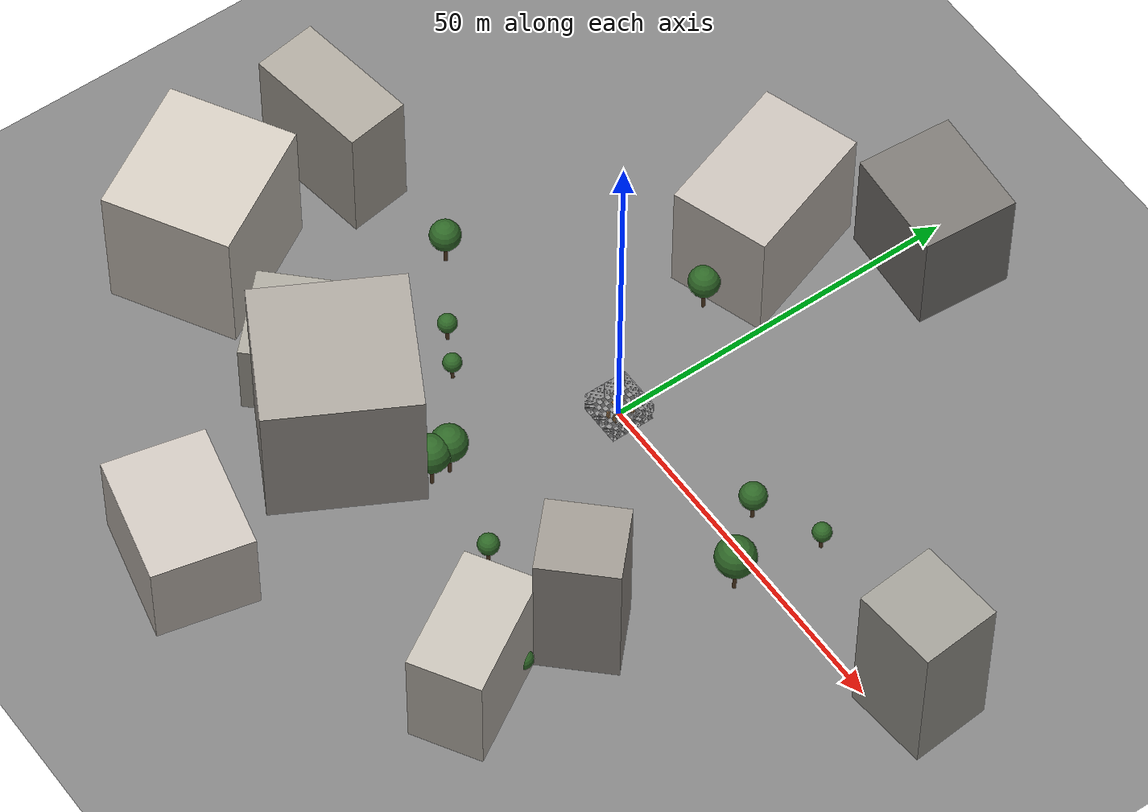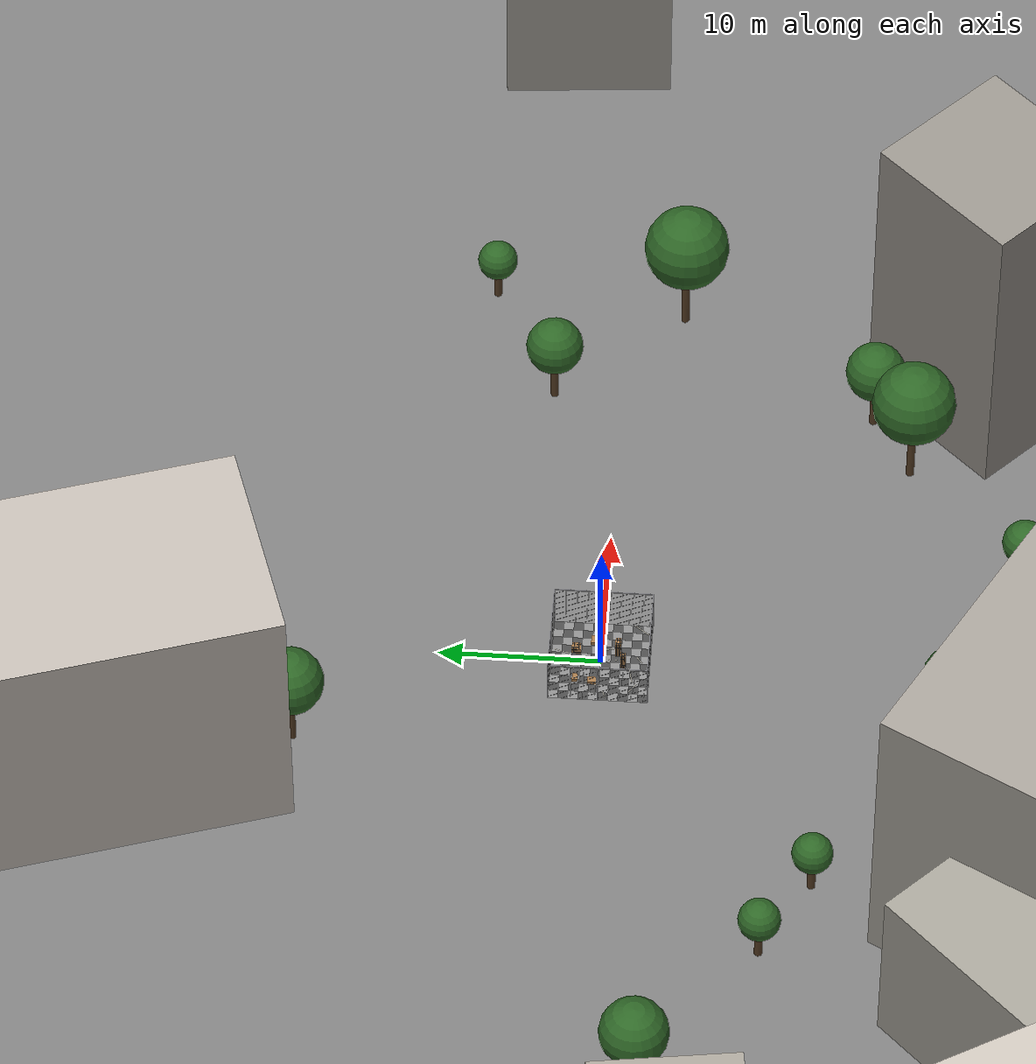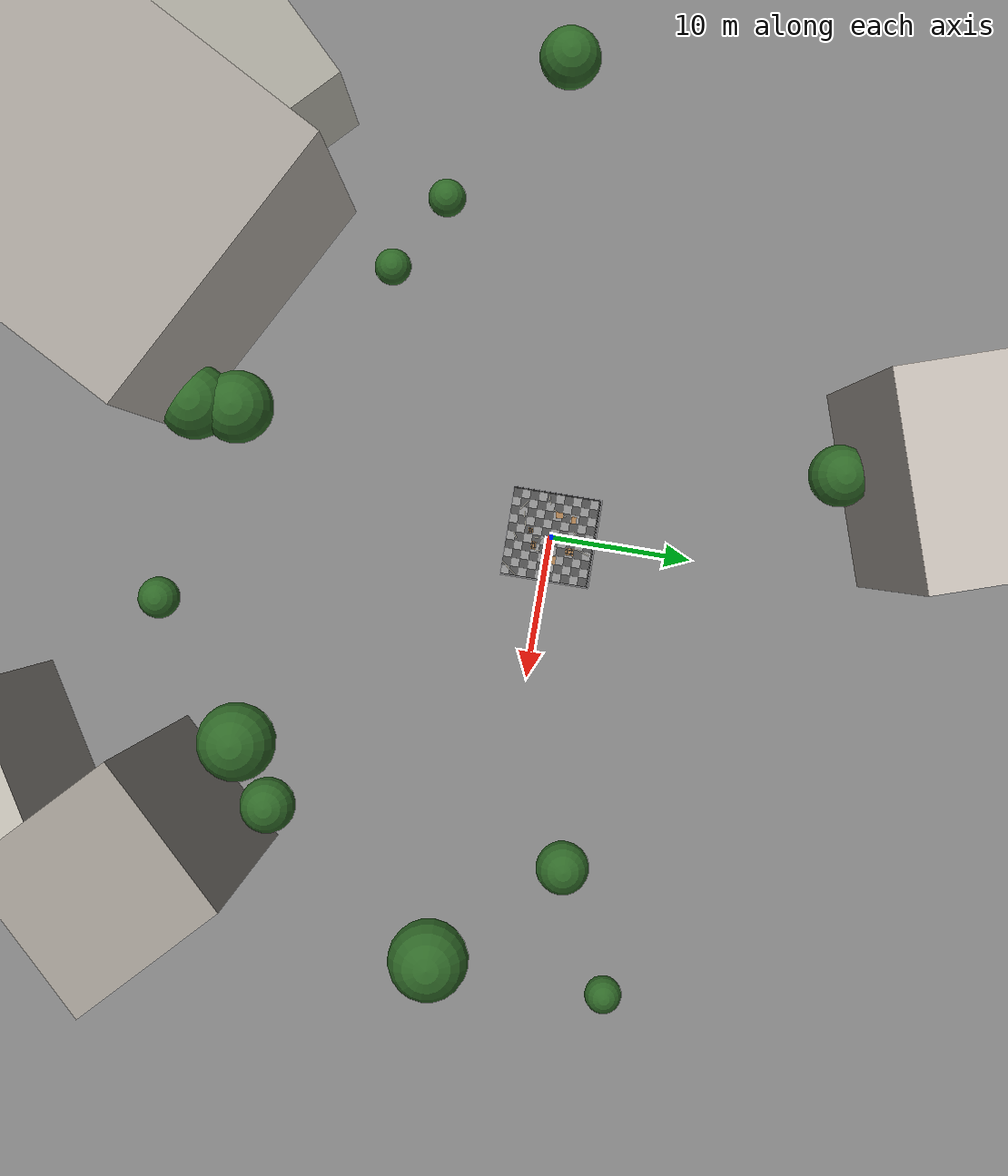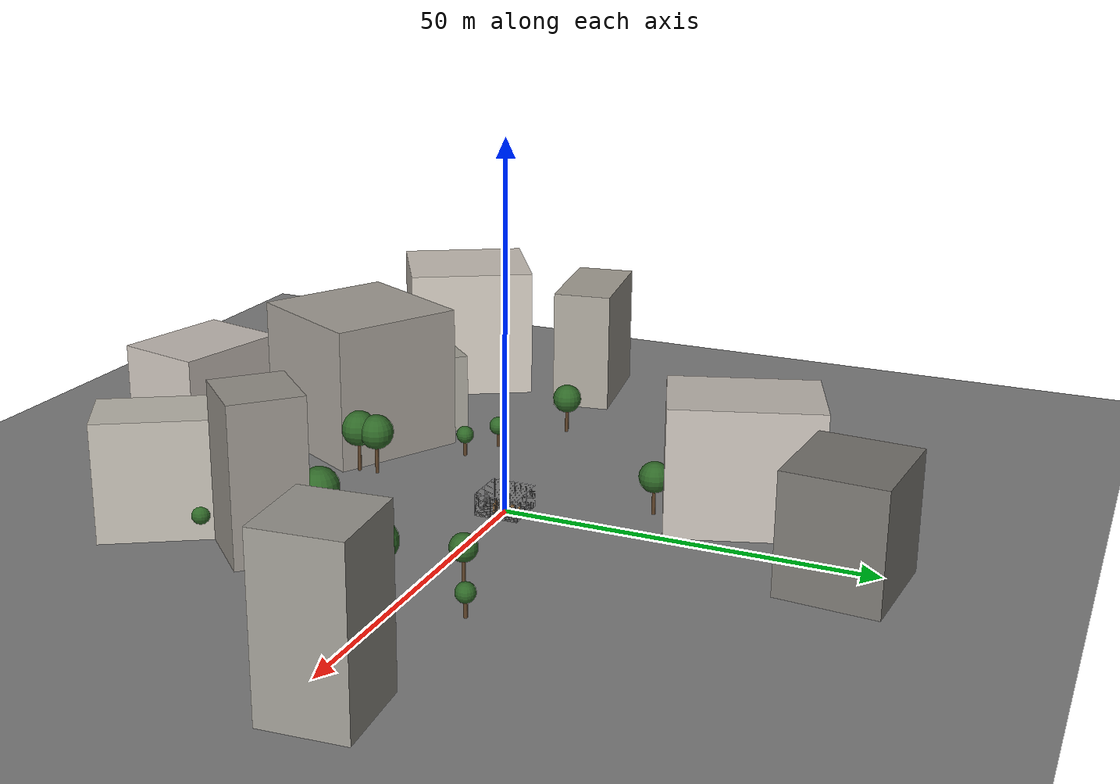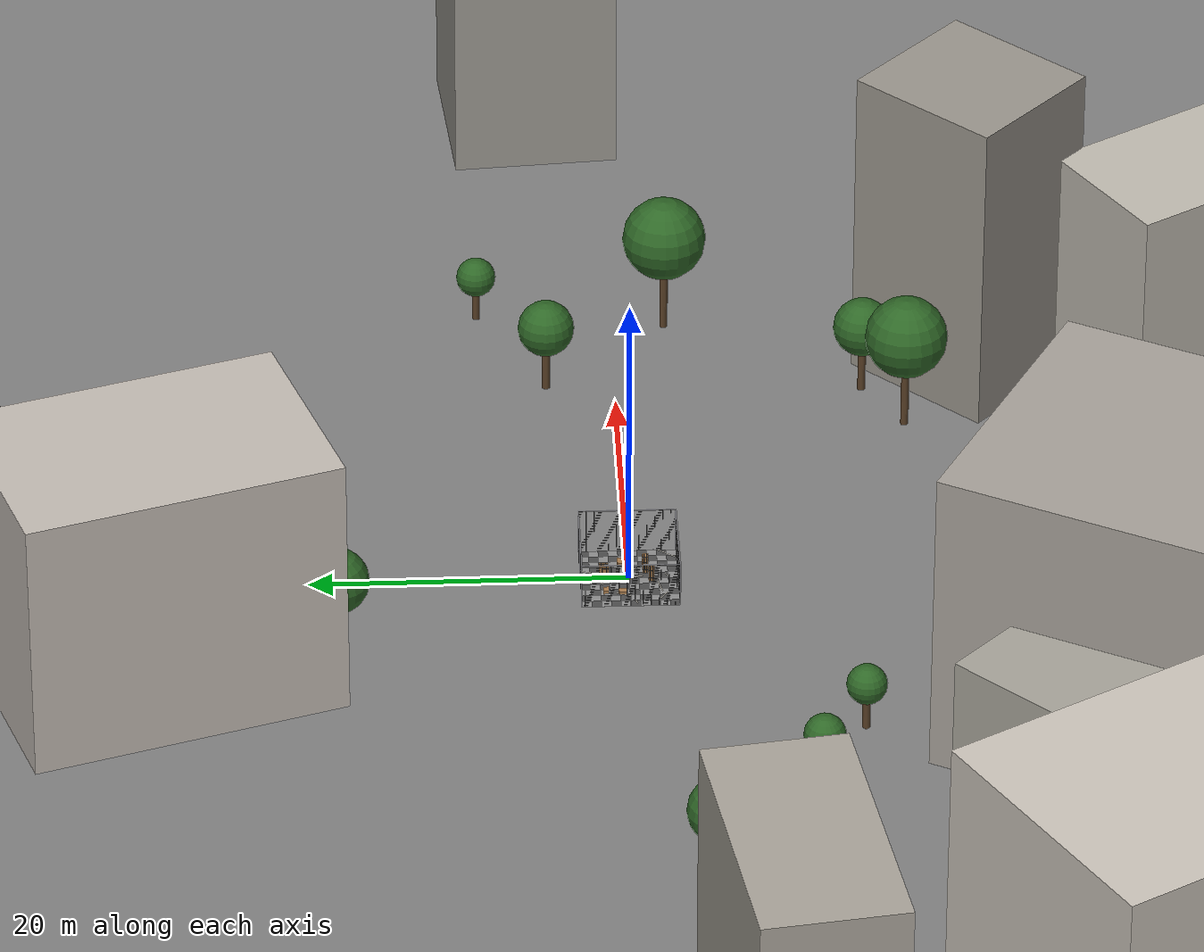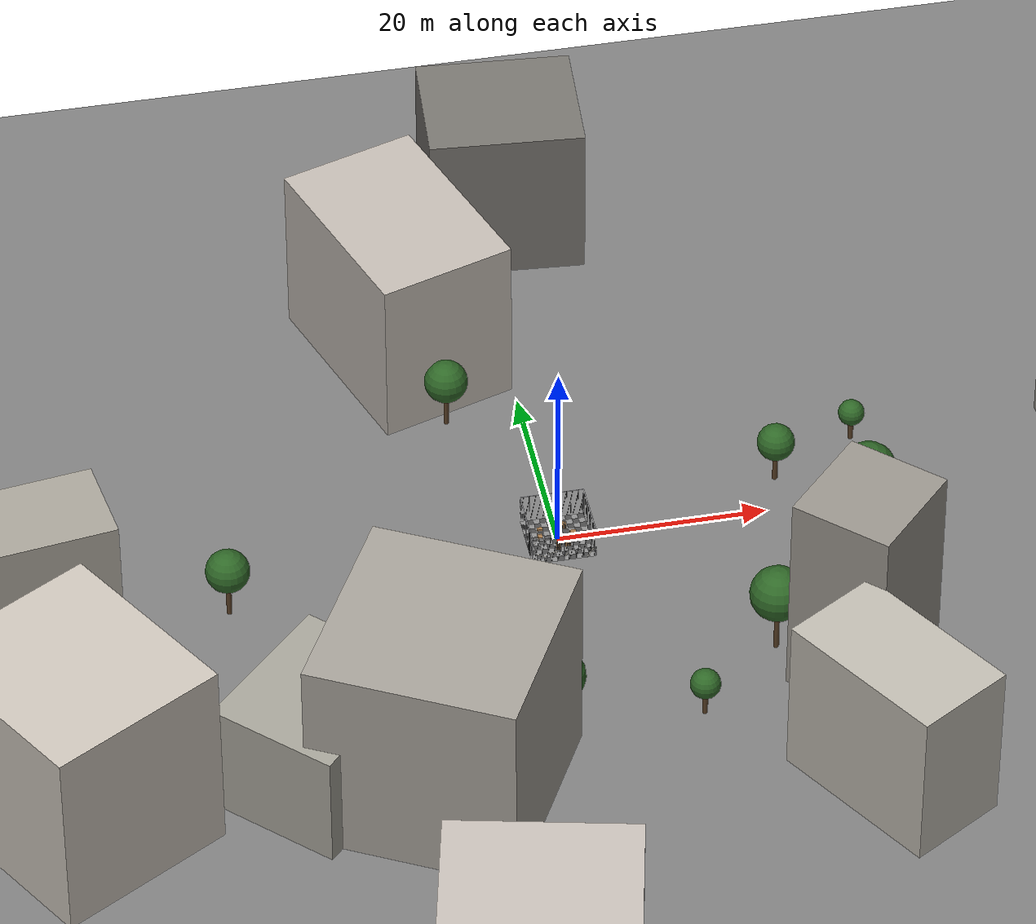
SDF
<sdf version="1.9">
 <world name="ecps295_lowbox_s8">
  <physics name="1ms" type="ignore">
   <max_step_size>0.001</max_step_size>
   <real_time_factor>1.0</real_time_factor>
  </physics>
  <plugin filename="gz-sim-physics-system" name="gz::sim::systems::Physics"/>
  <plugin filename="gz-sim-sensors-system" name="gz::sim::systems::Sensors">
   <render_engine>ogre2</render_engine>
  </plugin>
  <plugin filename="gz-sim-user-commands-system" name="gz::sim::systems::UserCommands"/>
  <plugin filename="gz-sim-scene-broadcaster-system" name="gz::sim::systems::SceneBroadcaster"/>
  <plugin filename="gz-sim-imu-system" name="gz::sim::systems::Imu"/>
  <plugin filename="gz-sim-navsat-system" name="gz::sim::systems::NavSat"/>
  <scene><ambient>1 1 1</ambient><background>0.8 0.8 0.8</background></scene>
  <spherical_coordinates>
   <latitude_deg>33.6430</latitude_deg>
   <longitude_deg>-117.8420</longitude_deg>
   <elevation>20</elevation>
   <heading_deg>0</heading_deg>
   <surface_model>EARTH_WGS84</surface_model>
  </spherical_coordinates>
  <light type="directional" name="sun">
   <pose>0 0 10 0 0 0</pose>
   <diffuse>0.8 0.8 0.8 1</diffuse>
   <specular>0.8 0.8 0.8 1</specular>
   <direction>-0.5 0.1 -0.9</direction>
  </light>
  <model name="ground_plane">
   <static>true</static>
   <link name="link">
    <collision name="collision">
     <geometry><plane><normal>0 0 1</normal><size>50 50</size></plane></geometry>
    </collision>
    <visual name="visual">
     <geometry><plane><normal>0 0 1</normal><size>50 50</size></plane></geometry>
     <material><ambient>0.5 0.5 0.5 1</ambient><diffuse>0.5 0.5 0.5 1</diffuse></material>
    </visual>
   </link>
  </model>
  <model name="eva_mat">
   <static>true</static>
   <link name="link">
    <visual name="t0_0">
     <pose>-2.745 -2.745 0.001 0 0 0</pose>
     <geometry><box><size>0.61 0.61 0.002</size></box></geometry>
     <material><ambient>0.3 0.3 0.3 1</ambient><diffuse>0.3 0.3 0.3 1</diffuse></material>
    </visual>
    <visual name="t0_1">
     <pose>-2.745 -2.135 0.001 0 0 0</pose>
     <geometry><box><size>0.61 0.61 0.002</size></box></geometry>
     <material><ambient>0.55 0.55 0.55 1</ambient><diffuse>0.55 0.55 0.55 1</diffuse></material>
    </visual>
    <visual name="t0_2">
     <pose>-2.745 -1.525 0.001 0 0 0</pose>
     <geometry><box><size>0.61 0.61 0.002</size></box></geometry>
     <material><ambient>0.3 0.3 0.3 1</ambient><diffuse>0.3 0.3 0.3 1</diffuse></material>
    </visual>
    <visual name="t0_3">
     <pose>-2.745 -0.915 0.001 0 0 0</pose>
     <geometry><box><size>0.61 0.61 0.002</size></box></geometry>
     <material><ambient>0.55 0.55 0.55 1</ambient><diffuse>0.55 0.55 0.55 1</diffuse></material>
    </visual>
    <visual name="t0_4">
     <pose>-2.745 -0.305 0.001 0 0 0</pose>
     <geometry><box><size>0.61 0.61 0.002</size></box></geometry>
     <material><ambient>0.3 0.3 0.3 1</ambient><diffuse>0.3 0.3 0.3 1</diffuse></material>
    </visual>
    <visual name="t0_5">
     <pose>-2.745 0.305 0.001 0 0 0</pose>
     <geometry><box><size>0.61 0.61 0.002</size></box></geometry>
     <material><ambient>0.55 0.55 0.55 1</ambient><diffuse>0.55 0.55 0.55 1</diffuse></material>
    </visual>
    <visual name="t0_6">
     <pose>-2.745 0.915 0.001 0 0 0</pose>
     <geometry><box><size>0.61 0.61 0.002</size></box></geometry>
     <material><ambient>0.3 0.3 0.3 1</ambient><diffuse>0.3 0.3 0.3 1</diffuse></material>
    </visual>
    <visual name="t0_7">
     <pose>-2.745 1.525 0.001 0 0 0</pose>
     <geometry><box><size>0.61 0.61 0.002</size></box></geometry>
     <material><ambient>0.55 0.55 0.55 1</ambient><diffuse>0.55 0.55 0.55 1</diffuse></material>
    </visual>
    <visual name="t0_8">
     <pose>-2.745 2.135 0.001 0 0 0</pose>
     <geometry><box><size>0.61 0.61 0.002</size></box></geometry>
     <material><ambient>0.3 0.3 0.3 1</ambient><diffuse>0.3 0.3 0.3 1</diffuse></material>
    </visual>
    <visual name="t0_9">
     <pose>-2.745 2.745 0.001 0 0 0</pose>
     <geometry><box><size>0.61 0.61 0.002</size></box></geometry>
     <material><ambient>0.55 0.55 0.55 1</ambient><diffuse>0.55 0.55 0.55 1</diffuse></material>
    </visual>
    <visual name="t1_0">
     <pose>-2.135 -2.745 0.001 0 0 0</pose>
     <geometry><box><size>0.61 0.61 0.002</size></box></geometry>
     <material><ambient>0.55 0.55 0.55 1</ambient><diffuse>0.55 0.55 0.55 1</diffuse></material>
    </visual>
    <visual name="t1_1">
     <pose>-2.135 -2.135 0.001 0 0 0</pose>
     <geometry><box><size>0.61 0.61 0.002</size></box></geometry>
     <material><ambient>0.3 0.3 0.3 1</ambient><diffuse>0.3 0.3 0.3 1</diffuse></material>
    </visual>
    <visual name="t1_2">
     <pose>-2.135 -1.525 0.001 0 0 0</pose>
     <geometry><box><size>0.61 0.61 0.002</size></box></geometry>
     <material><ambient>0.55 0.55 0.55 1</ambient><diffuse>0.55 0.55 0.55 1</diffuse></material>
    </visual>
    <visual name="t1_3">
     <pose>-2.135 -0.915 0.001 0 0 0</pose>
     <geometry><box><size>0.61 0.61 0.002</size></box></geometry>
     <material><ambient>0.3 0.3 0.3 1</ambient><diffuse>0.3 0.3 0.3 1</diffuse></material>
    </visual>
    <visual name="t1_4">
     <pose>-2.135 -0.305 0.001 0 0 0</pose>
     <geometry><box><size>0.61 0.61 0.002</size></box></geometry>
     <material><ambient>0.55 0.55 0.55 1</ambient><diffuse>0.55 0.55 0.55 1</diffuse></material>
    </visual>
    <visual name="t1_5">
     <pose>-2.135 0.305 0.001 0 0 0</pose>
     <geometry><box><size>0.61 0.61 0.002</size></box></geometry>
     <material><ambient>0.3 0.3 0.3 1</ambient><diffuse>0.3 0.3 0.3 1</diffuse></material>
    </visual>
    <visual name="t1_6">
     <pose>-2.135 0.915 0.001 0 0 0</pose>
     <geometry><box><size>0.61 0.61 0.002</size></box></geometry>
     <material><ambient>0.55 0.55 0.55 1</ambient><diffuse>0.55 0.55 0.55 1</diffuse></material>
    </visual>
    <visual name="t1_7">
     <pose>-2.135 1.525 0.001 0 0 0</pose>
     <geometry><box><size>0.61 0.61 0.002</size></box></geometry>
     <material><ambient>0.3 0.3 0.3 1</ambient><diffuse>0.3 0.3 0.3 1</diffuse></material>
    </visual>
    <visual name="t1_8">
     <pose>-2.135 2.135 0.001 0 0 0</pose>
     <geometry><box><size>0.61 0.61 0.002</size></box></geometry>
     <material><ambient>0.55 0.55 0.55 1</ambient><diffuse>0.55 0.55 0.55 1</diffuse></material>
    </visual>
    <visual name="t1_9">
     <pose>-2.135 2.745 0.001 0 0 0</pose>
     <geometry><box><size>0.61 0.61 0.002</size></box></geometry>
     <material><ambient>0.3 0.3 0.3 1</ambient><diffuse>0.3 0.3 0.3 1</diffuse></material>
    </visual>
    <visual name="t2_0">
     <pose>-1.525 -2.745 0.001 0 0 0</pose>
     <geometry><box><size>0.61 0.61 0.002</size></box></geometry>
     <material><ambient>0.3 0.3 0.3 1</ambient><diffuse>0.3 0.3 0.3 1</diffuse></material>
    </visual>
    <visual name="t2_1">
     <pose>-1.525 -2.135 0.001 0 0 0</pose>
     <geometry><box><size>0.61 0.61 0.002</size></box></geometry>
     <material><ambient>0.55 0.55 0.55 1</ambient><diffuse>0.55 0.55 0.55 1</diffuse></material>
    </visual>
    <visual name="t2_2">
     <pose>-1.525 -1.525 0.001 0 0 0</pose>
     <geometry><box><size>0.61 0.61 0.002</size></box></geometry>
     <material><ambient>0.3 0.3 0.3 1</ambient><diffuse>0.3 0.3 0.3 1</diffuse></material>
    </visual>
    <visual name="t2_3">
     <pose>-1.525 -0.915 0.001 0 0 0</pose>
     <geometry><box><size>0.61 0.61 0.002</size></box></geometry>
     <material><ambient>0.55 0.55 0.55 1</ambient><diffuse>0.55 0.55 0.55 1</diffuse></material>
    </visual>
    <visual name="t2_4">
     <pose>-1.525 -0.305 0.001 0 0 0</pose>
     <geometry><box><size>0.61 0.61 0.002</size></box></geometry>
     <material><ambient>0.3 0.3 0.3 1</ambient><diffuse>0.3 0.3 0.3 1</diffuse></material>
    </visual>
    <visual name="t2_5">
     <pose>-1.525 0.305 0.001 0 0 0</pose>
     <geometry><box><size>0.61 0.61 0.002</size></box></geometry>
     <material><ambient>0.55 0.55 0.55 1</ambient><diffuse>0.55 0.55 0.55 1</diffuse></material>
    </visual>
    <visual name="t2_6">
     <pose>-1.525 0.915 0.001 0 0 0</pose>
     <geometry><box><size>0.61 0.61 0.002</size></box></geometry>
     <material><ambient>0.3 0.3 0.3 1</ambient><diffuse>0.3 0.3 0.3 1</diffuse></material>
    </visual>
    <visual name="t2_7">
     <pose>-1.525 1.525 0.001 0 0 0</pose>
     <geometry><box><size>0.61 0.61 0.002</size></box></geometry>
     <material><ambient>0.55 0.55 0.55 1</ambient><diffuse>0.55 0.55 0.55 1</diffuse></material>
    </visual>
    <visual name="t2_8">
     <pose>-1.525 2.135 0.001 0 0 0</pose>
     <geometry><box><size>0.61 0.61 0.002</size></box></geometry>
     <material><ambient>0.3 0.3 0.3 1</ambient><diffuse>0.3 0.3 0.3 1</diffuse></material>
    </visual>
    <visual name="t2_9">
     <pose>-1.525 2.745 0.001 0 0 0</pose>
     <geometry><box><size>0.61 0.61 0.002</size></box></geometry>
     <material><ambient>0.55 0.55 0.55 1</ambient><diffuse>0.55 0.55 0.55 1</diffuse></material>
    </visual>
    <visual name="t3_0">
     <pose>-0.915 -2.745 0.001 0 0 0</pose>
     <geometry><box><size>0.61 0.61 0.002</size></box></geometry>
     <material><ambient>0.55 0.55 0.55 1</ambient><diffuse>0.55 0.55 0.55 1</diffuse></material>
    </visual>
    <visual name="t3_1">
     <pose>-0.915 -2.135 0.001 0 0 0</pose>
     <geometry><box><size>0.61 0.61 0.002</size></box></geometry>
     <material><ambient>0.3 0.3 0.3 1</ambient><diffuse>0.3 0.3 0.3 1</diffuse></material>
    </visual>
    <visual name="t3_2">
     <pose>-0.915 -1.525 0.001 0 0 0</pose>
     <geometry><box><size>0.61 0.61 0.002</size></box></geometry>
     <material><ambient>0.55 0.55 0.55 1</ambient><diffuse>0.55 0.55 0.55 1</diffuse></material>
    </visual>
    <visual name="t3_3">
     <pose>-0.915 -0.915 0.001 0 0 0</pose>
     <geometry><box><size>0.61 0.61 0.002</size></box></geometry>
     <material><ambient>0.3 0.3 0.3 1</ambient><diffuse>0.3 0.3 0.3 1</diffuse></material>
    </visual>
    <visual name="t3_4">
     <pose>-0.915 -0.305 0.001 0 0 0</pose>
     <geometry><box><size>0.61 0.61 0.002</size></box></geometry>
     <material><ambient>0.55 0.55 0.55 1</ambient><diffuse>0.55 0.55 0.55 1</diffuse></material>
    </visual>
    <visual name="t3_5">
     <pose>-0.915 0.305 0.001 0 0 0</pose>
     <geometry><box><size>0.61 0.61 0.002</size></box></geometry>
     <material><ambient>0.3 0.3 0.3 1</ambient><diffuse>0.3 0.3 0.3 1</diffuse></material>
    </visual>
    <visual name="t3_6">
     <pose>-0.915 0.915 0.001 0 0 0</pose>
     <geometry><box><size>0.61 0.61 0.002</size></box></geometry>
     <material><ambient>0.55 0.55 0.55 1</ambient><diffuse>0.55 0.55 0.55 1</diffuse></material>
    </visual>
    <visual name="t3_7">
     <pose>-0.915 1.525 0.001 0 0 0</pose>
     <geometry><box><size>0.61 0.61 0.002</size></box></geometry>
     <material><ambient>0.3 0.3 0.3 1</ambient><diffuse>0.3 0.3 0.3 1</diffuse></material>
    </visual>
    <visual name="t3_8">
     <pose>-0.915 2.135 0.001 0 0 0</pose>
     <geometry><box><size>0.61 0.61 0.002</size></box></geometry>
     <material><ambient>0.55 0.55 0.55 1</ambient><diffuse>0.55 0.55 0.55 1</diffuse></material>
    </visual>
    <visual name="t3_9">
     <pose>-0.915 2.745 0.001 0 0 0</pose>
     <geometry><box><size>0.61 0.61 0.002</size></box></geometry>
     <material><ambient>0.3 0.3 0.3 1</ambient><diffuse>0.3 0.3 0.3 1</diffuse></material>
    </visual>
    <visual name="t4_0">
     <pose>-0.305 -2.745 0.001 0 0 0</pose>
     <geometry><box><size>0.61 0.61 0.002</size></box></geometry>
     <material><ambient>0.3 0.3 0.3 1</ambient><diffuse>0.3 0.3 0.3 1</diffuse></material>
    </visual>
    <visual name="t4_1">
     <pose>-0.305 -2.135 0.001 0 0 0</pose>
     <geometry><box><size>0.61 0.61 0.002</size></box></geometry>
     <material><ambient>0.55 0.55 0.55 1</ambient><diffuse>0.55 0.55 0.55 1</diffuse></material>
    </visual>
    <visual name="t4_2">
     <pose>-0.305 -1.525 0.001 0 0 0</pose>
     <geometry><box><size>0.61 0.61 0.002</size></box></geometry>
     <material><ambient>0.3 0.3 0.3 1</ambient><diffuse>0.3 0.3 0.3 1</diffuse></material>
    </visual>
    <visual name="t4_3">
     <pose>-0.305 -0.915 0.001 0 0 0</pose>
     <geometry><box><size>0.61 0.61 0.002</size></box></geometry>
     <material><ambient>0.55 0.55 0.55 1</ambient><diffuse>0.55 0.55 0.55 1</diffuse></material>
    </visual>
    <visual name="t4_4">
     <pose>-0.305 -0.305 0.001 0 0 0</pose>
     <geometry><box><size>0.61 0.61 0.002</size></box></geometry>
     <material><ambient>0.3 0.3 0.3 1</ambient><diffuse>0.3 0.3 0.3 1</diffuse></material>
    </visual>
    <visual name="t4_5">
     <pose>-0.305 0.305 0.001 0 0 0</pose>
     <geometry><box><size>0.61 0.61 0.002</size></box></geometry>
     <material><ambient>0.55 0.55 0.55 1</ambient><diffuse>0.55 0.55 0.55 1</diffuse></material>
    </visual>
    <visual name="t4_6">
     <pose>-0.305 0.915 0.001 0 0 0</pose>
     <geometry><box><size>0.61 0.61 0.002</size></box></geometry>
     <material><ambient>0.3 0.3 0.3 1</ambient><diffuse>0.3 0.3 0.3 1</diffuse></material>
    </visual>
    <visual name="t4_7">
     <pose>-0.305 1.525 0.001 0 0 0</pose>
     <geometry><box><size>0.61 0.61 0.002</size></box></geometry>
     <material><ambient>0.55 0.55 0.55 1</ambient><diffuse>0.55 0.55 0.55 1</diffuse></material>
    </visual>
    <visual name="t4_8">
     <pose>-0.305 2.135 0.001 0 0 0</pose>
     <geometry><box><size>0.61 0.61 0.002</size></box></geometry>
     <material><ambient>0.3 0.3 0.3 1</ambient><diffuse>0.3 0.3 0.3 1</diffuse></material>
    </visual>
    <visual name="t4_9">
     <pose>-0.305 2.745 0.001 0 0 0</pose>
     <geometry><box><size>0.61 0.61 0.002</size></box></geometry>
     <material><ambient>0.55 0.55 0.55 1</ambient><diffuse>0.55 0.55 0.55 1</diffuse></material>
    </visual>
    <visual name="t5_0">
     <pose>0.305 -2.745 0.001 0 0 0</pose>
     <geometry><box><size>0.61 0.61 0.002</size></box></geometry>
     <material><ambient>0.55 0.55 0.55 1</ambient><diffuse>0.55 0.55 0.55 1</diffuse></material>
    </visual>
    <visual name="t5_1">
     <pose>0.305 -2.135 0.001 0 0 0</pose>
     <geometry><box><size>0.61 0.61 0.002</size></box></geometry>
     <material><ambient>0.3 0.3 0.3 1</ambient><diffuse>0.3 0.3 0.3 1</diffuse></material>
    </visual>
    <visual name="t5_2">
     <pose>0.305 -1.525 0.001 0 0 0</pose>
     <geometry><box><size>0.61 0.61 0.002</size></box></geometry>
     <material><ambient>0.55 0.55 0.55 1</ambient><diffuse>0.55 0.55 0.55 1</diffuse></material>
    </visual>
    <visual name="t5_3">
     <pose>0.305 -0.915 0.001 0 0 0</pose>
     <geometry><box><size>0.61 0.61 0.002</size></box></geometry>
     <material><ambient>0.3 0.3 0.3 1</ambient><diffuse>0.3 0.3 0.3 1</diffuse></material>
    </visual>
    <visual name="t5_4">
     <pose>0.305 -0.305 0.001 0 0 0</pose>
     <geometry><box><size>0.61 0.61 0.002</size></box></geometry>
     <material><ambient>0.55 0.55 0.55 1</ambient><diffuse>0.55 0.55 0.55 1</diffuse></material>
    </visual>
    <visual name="t5_5">
     <pose>0.305 0.305 0.001 0 0 0</pose>
     <geometry><box><size>0.61 0.61 0.002</size></box></geometry>
     <material><ambient>0.3 0.3 0.3 1</ambient><diffuse>0.3 0.3 0.3 1</diffuse></material>
    </visual>
    <visual name="t5_6">
     <pose>0.305 0.915 0.001 0 0 0</pose>
     <geometry><box><size>0.61 0.61 0.002</size></box></geometry>
     <material><ambient>0.55 0.55 0.55 1</ambient><diffuse>0.55 0.55 0.55 1</diffuse></material>
    </visual>
    <visual name="t5_7">
     <pose>0.305 1.525 0.001 0 0 0</pose>
     <geometry><box><size>0.61 0.61 0.002</size></box></geometry>
     <material><ambient>0.3 0.3 0.3 1</ambient><diffuse>0.3 0.3 0.3 1</diffuse></material>
    </visual>
    <visual name="t5_8">
     <pose>0.305 2.135 0.001 0 0 0</pose>
     <geometry><box><size>0.61 0.61 0.002</size></box></geometry>
     <material><ambient>0.55 0.55 0.55 1</ambient><diffuse>0.55 0.55 0.55 1</diffuse></material>
    </visual>
    <visual name="t5_9">
     <pose>0.305 2.745 0.001 0 0 0</pose>
     <geometry><box><size>0.61 0.61 0.002</size></box></geometry>
     <material><ambient>0.3 0.3 0.3 1</ambient><diffuse>0.3 0.3 0.3 1</diffuse></material>
    </visual>
    <visual name="t6_0">
     <pose>0.915 -2.745 0.001 0 0 0</pose>
     <geometry><box><size>0.61 0.61 0.002</size></box></geometry>
     <material><ambient>0.3 0.3 0.3 1</ambient><diffuse>0.3 0.3 0.3 1</diffuse></material>
    </visual>
    <visual name="t6_1">
     <pose>0.915 -2.135 0.001 0 0 0</pose>
     <geometry><box><size>0.61 0.61 0.002</size></box></geometry>
     <material><ambient>0.55 0.55 0.55 1</ambient><diffuse>0.55 0.55 0.55 1</diffuse></material>
    </visual>
    <visual name="t6_2">
     <pose>0.915 -1.525 0.001 0 0 0</pose>
     <geometry><box><size>0.61 0.61 0.002</size></box></geometry>
     <material><ambient>0.3 0.3 0.3 1</ambient><diffuse>0.3 0.3 0.3 1</diffuse></material>
    </visual>
    <visual name="t6_3">
     <pose>0.915 -0.915 0.001 0 0 0</pose>
     <geometry><box><size>0.61 0.61 0.002</size></box></geometry>
     <material><ambient>0.55 0.55 0.55 1</ambient><diffuse>0.55 0.55 0.55 1</diffuse></material>
    </visual>
    <visual name="t6_4">
     <pose>0.915 -0.305 0.001 0 0 0</pose>
     <geometry><box><size>0.61 0.61 0.002</size></box></geometry>
     <material><ambient>0.3 0.3 0.3 1</ambient><diffuse>0.3 0.3 0.3 1</diffuse></material>
    </visual>
    <visual name="t6_5">
     <pose>0.915 0.305 0.001 0 0 0</pose>
     <geometry><box><size>0.61 0.61 0.002</size></box></geometry>
     <material><ambient>0.55 0.55 0.55 1</ambient><diffuse>0.55 0.55 0.55 1</diffuse></material>
    </visual>
    <visual name="t6_6">
     <pose>0.915 0.915 0.001 0 0 0</pose>
     <geometry><box><size>0.61 0.61 0.002</size></box></geometry>
     <material><ambient>0.3 0.3 0.3 1</ambient><diffuse>0.3 0.3 0.3 1</diffuse></material>
    </visual>
    <visual name="t6_7">
     <pose>0.915 1.525 0.001 0 0 0</pose>
     <geometry><box><size>0.61 0.61 0.002</size></box></geometry>
     <material><ambient>0.55 0.55 0.55 1</ambient><diffuse>0.55 0.55 0.55 1</diffuse></material>
    </visual>
    <visual name="t6_8">
     <pose>0.915 2.135 0.001 0 0 0</pose>
     <geometry><box><size>0.61 0.61 0.002</size></box></geometry>
     <material><ambient>0.3 0.3 0.3 1</ambient><diffuse>0.3 0.3 0.3 1</diffuse></material>
    </visual>
    <visual name="t6_9">
     <pose>0.915 2.745 0.001 0 0 0</pose>
     <geometry><box><size>0.61 0.61 0.002</size></box></geometry>
     <material><ambient>0.55 0.55 0.55 1</ambient><diffuse>0.55 0.55 0.55 1</diffuse></material>
    </visual>
    <visual name="t7_0">
     <pose>1.525 -2.745 0.001 0 0 0</pose>
     <geometry><box><size>0.61 0.61 0.002</size></box></geometry>
     <material><ambient>0.55 0.55 0.55 1</ambient><diffuse>0.55 0.55 0.55 1</diffuse></material>
    </visual>
    <visual name="t7_1">
     <pose>1.525 -2.135 0.001 0 0 0</pose>
     <geometry><box><size>0.61 0.61 0.002</size></box></geometry>
     <material><ambient>0.3 0.3 0.3 1</ambient><diffuse>0.3 0.3 0.3 1</diffuse></material>
    </visual>
    <visual name="t7_2">
     <pose>1.525 -1.525 0.001 0 0 0</pose>
     <geometry><box><size>0.61 0.61 0.002</size></box></geometry>
     <material><ambient>0.55 0.55 0.55 1</ambient><diffuse>0.55 0.55 0.55 1</diffuse></material>
    </visual>
    <visual name="t7_3">
     <pose>1.525 -0.915 0.001 0 0 0</pose>
     <geometry><box><size>0.61 0.61 0.002</size></box></geometry>
     <material><ambient>0.3 0.3 0.3 1</ambient><diffuse>0.3 0.3 0.3 1</diffuse></material>
    </visual>
    <visual name="t7_4">
     <pose>1.525 -0.305 0.001 0 0 0</pose>
     <geometry><box><size>0.61 0.61 0.002</size></box></geometry>
     <material><ambient>0.55 0.55 0.55 1</ambient><diffuse>0.55 0.55 0.55 1</diffuse></material>
    </visual>
    <visual name="t7_5">
     <pose>1.525 0.305 0.001 0 0 0</pose>
     <geometry><box><size>0.61 0.61 0.002</size></box></geometry>
     <material><ambient>0.3 0.3 0.3 1</ambient><diffuse>0.3 0.3 0.3 1</diffuse></material>
    </visual>
    <visual name="t7_6">
     <pose>1.525 0.915 0.001 0 0 0</pose>
     <geometry><box><size>0.61 0.61 0.002</size></box></geometry>
     <material><ambient>0.55 0.55 0.55 1</ambient><diffuse>0.55 0.55 0.55 1</diffuse></material>
    </visual>
    <visual name="t7_7">
     <pose>1.525 1.525 0.001 0 0 0</pose>
     <geometry><box><size>0.61 0.61 0.002</size></box></geometry>
     <material><ambient>0.3 0.3 0.3 1</ambient><diffuse>0.3 0.3 0.3 1</diffuse></material>
    </visual>
    <visual name="t7_8">
     <pose>1.525 2.135 0.001 0 0 0</pose>
     <geometry><box><size>0.61 0.61 0.002</size></box></geometry>
     <material><ambient>0.55 0.55 0.55 1</ambient><diffuse>0.55 0.55 0.55 1</diffuse></material>
    </visual>
    <visual name="t7_9">
     <pose>1.525 2.745 0.001 0 0 0</pose>
     <geometry><box><size>0.61 0.61 0.002</size></box></geometry>
     <material><ambient>0.3 0.3 0.3 1</ambient><diffuse>0.3 0.3 0.3 1</diffuse></material>
    </visual>
    <visual name="t8_0">
     <pose>2.135 -2.745 0.001 0 0 0</pose>
     <geometry><box><size>0.61 0.61 0.002</size></box></geometry>
     <material><ambient>0.3 0.3 0.3 1</ambient><diffuse>0.3 0.3 0.3 1</diffuse></material>
    </visual>
    <visual name="t8_1">
     <pose>2.135 -2.135 0.001 0 0 0</pose>
     <geometry><box><size>0.61 0.61 0.002</size></box></geometry>
     <material><ambient>0.55 0.55 0.55 1</ambient><diffuse>0.55 0.55 0.55 1</diffuse></material>
    </visual>
    <visual name="t8_2">
     <pose>2.135 -1.525 0.001 0 0 0</pose>
     <geometry><box><size>0.61 0.61 0.002</size></box></geometry>
     <material><ambient>0.3 0.3 0.3 1</ambient><diffuse>0.3 0.3 0.3 1</diffuse></material>
    </visual>
    <visual name="t8_3">
     <pose>2.135 -0.915 0.001 0 0 0</pose>
     <geometry><box><size>0.61 0.61 0.002</size></box></geometry>
     <material><ambient>0.55 0.55 0.55 1</ambient><diffuse>0.55 0.55 0.55 1</diffuse></material>
    </visual>
    <visual name="t8_4">
     <pose>2.135 -0.305 0.001 0 0 0</pose>
     <geometry><box><size>0.61 0.61 0.002</size></box></geometry>
     <material><ambient>0.3 0.3 0.3 1</ambient><diffuse>0.3 0.3 0.3 1</diffuse></material>
    </visual>
    <visual name="t8_5">
     <pose>2.135 0.305 0.001 0 0 0</pose>
     <geometry><box><size>0.61 0.61 0.002</size></box></geometry>
     <material><ambient>0.55 0.55 0.55 1</ambient><diffuse>0.55 0.55 0.55 1</diffuse></material>
    </visual>
    <visual name="t8_6">
     <pose>2.135 0.915 0.001 0 0 0</pose>
     <geometry><box><size>0.61 0.61 0.002</size></box></geometry>
     <material><ambient>0.3 0.3 0.3 1</ambient><diffuse>0.3 0.3 0.3 1</diffuse></material>
    </visual>
    <visual name="t8_7">
     <pose>2.135 1.525 0.001 0 0 0</pose>
     <geometry><box><size>0.61 0.61 0.002</size></box></geometry>
     <material><ambient>0.55 0.55 0.55 1</ambient><diffuse>0.55 0.55 0.55 1</diffuse></material>
    </visual>
    <visual name="t8_8">
     <pose>2.135 2.135 0.001 0 0 0</pose>
     <geometry><box><size>0.61 0.61 0.002</size></box></geometry>
     <material><ambient>0.3 0.3 0.3 1</ambient><diffuse>0.3 0.3 0.3 1</diffuse></material>
    </visual>
    <visual name="t8_9">
     <pose>2.135 2.745 0.001 0 0 0</pose>
     <geometry><box><size>0.61 0.61 0.002</size></box></geometry>
     <material><ambient>0.55 0.55 0.55 1</ambient><diffuse>0.55 0.55 0.55 1</diffuse></material>
    </visual>
    <visual name="t9_0">
     <pose>2.745 -2.745 0.001 0 0 0</pose>
     <geometry><box><size>0.61 0.61 0.002</size></box></geometry>
     <material><ambient>0.55 0.55 0.55 1</ambient><diffuse>0.55 0.55 0.55 1</diffuse></material>
    </visual>
    <visual name="t9_1">
     <pose>2.745 -2.135 0.001 0 0 0</pose>
     <geometry><box><size>0.61 0.61 0.002</size></box></geometry>
     <material><ambient>0.3 0.3 0.3 1</ambient><diffuse>0.3 0.3 0.3 1</diffuse></material>
    </visual>
    <visual name="t9_2">
     <pose>2.745 -1.525 0.001 0 0 0</pose>
     <geometry><box><size>0.61 0.61 0.002</size></box></geometry>
     <material><ambient>0.55 0.55 0.55 1</ambient><diffuse>0.55 0.55 0.55 1</diffuse></material>
    </visual>
    <visual name="t9_3">
     <pose>2.745 -0.915 0.001 0 0 0</pose>
     <geometry><box><size>0.61 0.61 0.002</size></box></geometry>
     <material><ambient>0.3 0.3 0.3 1</ambient><diffuse>0.3 0.3 0.3 1</diffuse></material>
    </visual>
    <visual name="t9_4">
     <pose>2.745 -0.305 0.001 0 0 0</pose>
     <geometry><box><size>0.61 0.61 0.002</size></box></geometry>
     <material><ambient>0.55 0.55 0.55 1</ambient><diffuse>0.55 0.55 0.55 1</diffuse></material>
    </visual>
    <visual name="t9_5">
     <pose>2.745 0.305 0.001 0 0 0</pose>
     <geometry><box><size>0.61 0.61 0.002</size></box></geometry>
     <material><ambient>0.3 0.3 0.3 1</ambient><diffuse>0.3 0.3 0.3 1</diffuse></material>
    </visual>
    <visual name="t9_6">
     <pose>2.745 0.915 0.001 0 0 0</pose>
     <geometry><box><size>0.61 0.61 0.002</size></box></geometry>
     <material><ambient>0.55 0.55 0.55 1</ambient><diffuse>0.55 0.55 0.55 1</diffuse></material>
    </visual>
    <visual name="t9_7">
     <pose>2.745 1.525 0.001 0 0 0</pose>
     <geometry><box><size>0.61 0.61 0.002</size></box></geometry>
     <material><ambient>0.3 0.3 0.3 1</ambient><diffuse>0.3 0.3 0.3 1</diffuse></material>
    </visual>
    <visual name="t9_8">
     <pose>2.745 2.135 0.001 0 0 0</pose>
     <geometry><box><size>0.61 0.61 0.002</size></box></geometry>
     <material><ambient>0.55 0.55 0.55 1</ambient><diffuse>0.55 0.55 0.55 1</diffuse></material>
    </visual>
    <visual name="t9_9">
     <pose>2.745 2.745 0.001 0 0 0</pose>
     <geometry><box><size>0.61 0.61 0.002</size></box></geometry>
     <material><ambient>0.3 0.3 0.3 1</ambient><diffuse>0.3 0.3 0.3 1</diffuse></material>
    </visual>
   </link>
  </model>
  <model name="floor_tape">
   <static>true</static>
   <link name="link">
    <visual name="tape0">
     <pose>-0.969 -1.920 0.003 0 0 0.2276</pose>
     <geometry><box><size>1.086 0.050 0.001</size></box></geometry>
     <material><ambient>0.82 0.80 0.74 1</ambient><diffuse>0.82 0.80 0.74 1</diffuse></material>
    </visual>
    <visual name="tape1">
     <pose>0.197 -0.739 0.003 0 0 1.5942</pose>
     <geometry><box><size>0.552 0.050 0.001</size></box></geometry>
     <material><ambient>0.82 0.80 0.74 1</ambient><diffuse>0.82 0.80 0.74 1</diffuse></material>
    </visual>
    <visual name="tape2">
     <pose>-2.544 -0.365 0.003 0 0 0.2850</pose>
     <geometry><box><size>0.563 0.050 0.001</size></box></geometry>
     <material><ambient>0.82 0.80 0.74 1</ambient><diffuse>0.82 0.80 0.74 1</diffuse></material>
    </visual>
    <visual name="tape3">
     <pose>-0.415 1.798 0.003 0 0 0.7013</pose>
     <geometry><box><size>0.611 0.050 0.001</size></box></geometry>
     <material><ambient>0.82 0.80 0.74 1</ambient><diffuse>0.82 0.80 0.74 1</diffuse></material>
    </visual>
    <visual name="tape4">
     <pose>0.701 2.462 0.003 0 0 1.2462</pose>
     <geometry><box><size>1.019 0.050 0.001</size></box></geometry>
     <material><ambient>0.82 0.80 0.74 1</ambient><diffuse>0.82 0.80 0.74 1</diffuse></material>
    </visual>
    <visual name="tape5">
     <pose>2.619 -2.494 0.003 0 0 0.9098</pose>
     <geometry><box><size>1.273 0.050 0.001</size></box></geometry>
     <material><ambient>0.82 0.80 0.74 1</ambient><diffuse>0.82 0.80 0.74 1</diffuse></material>
    </visual>
    <visual name="tape6">
     <pose>-1.957 -2.102 0.003 0 0 2.5639</pose>
     <geometry><box><size>0.778 0.050 0.001</size></box></geometry>
     <material><ambient>0.82 0.80 0.74 1</ambient><diffuse>0.82 0.80 0.74 1</diffuse></material>
    </visual>
    <visual name="tape7">
     <pose>-1.756 0.449 0.003 0 0 1.1699</pose>
     <geometry><box><size>1.075 0.050 0.001</size></box></geometry>
     <material><ambient>0.82 0.80 0.74 1</ambient><diffuse>0.82 0.80 0.74 1</diffuse></material>
    </visual>
    <visual name="tape8">
     <pose>0.263 -2.405 0.003 0 0 0.6470</pose>
     <geometry><box><size>0.554 0.050 0.001</size></box></geometry>
     <material><ambient>0.82 0.80 0.74 1</ambient><diffuse>0.82 0.80 0.74 1</diffuse></material>
    </visual>
    <visual name="tape9">
     <pose>0.992 -0.398 0.003 0 0 1.8396</pose>
     <geometry><box><size>0.783 0.050 0.001</size></box></geometry>
     <material><ambient>0.82 0.80 0.74 1</ambient><diffuse>0.82 0.80 0.74 1</diffuse></material>
    </visual>
   </link>
  </model>
  <model name="cage_frame">
   <static>true</static>
   <link name="link">
    <visual name="post0_0">
     <pose>-3.050 -3.050 1.525 0 0 0.0000</pose>
     <geometry><box><size>0.050 0.050 3.050</size></box></geometry>
     <material><ambient>0.72 0.72 0.74 1</ambient><diffuse>0.72 0.72 0.74 1</diffuse></material>
    </visual>
    <visual name="post0_1">
     <pose>-3.050 0.000 1.525 0 0 0.0000</pose>
     <geometry><box><size>0.050 0.050 3.050</size></box></geometry>
     <material><ambient>0.72 0.72 0.74 1</ambient><diffuse>0.72 0.72 0.74 1</diffuse></material>
    </visual>
    <visual name="post0_2">
     <pose>-3.050 3.050 1.525 0 0 0.0000</pose>
     <geometry><box><size>0.050 0.050 3.050</size></box></geometry>
     <material><ambient>0.72 0.72 0.74 1</ambient><diffuse>0.72 0.72 0.74 1</diffuse></material>
    </visual>
    <visual name="post1_0">
     <pose>0.000 -3.050 1.525 0 0 0.0000</pose>
     <geometry><box><size>0.050 0.050 3.050</size></box></geometry>
     <material><ambient>0.72 0.72 0.74 1</ambient><diffuse>0.72 0.72 0.74 1</diffuse></material>
    </visual>
    <visual name="post1_2">
     <pose>0.000 3.050 1.525 0 0 0.0000</pose>
     <geometry><box><size>0.050 0.050 3.050</size></box></geometry>
     <material><ambient>0.72 0.72 0.74 1</ambient><diffuse>0.72 0.72 0.74 1</diffuse></material>
    </visual>
    <visual name="post2_0">
     <pose>3.050 -3.050 1.525 0 0 0.0000</pose>
     <geometry><box><size>0.050 0.050 3.050</size></box></geometry>
     <material><ambient>0.72 0.72 0.74 1</ambient><diffuse>0.72 0.72 0.74 1</diffuse></material>
    </visual>
    <visual name="post2_1">
     <pose>3.050 0.000 1.525 0 0 0.0000</pose>
     <geometry><box><size>0.050 0.050 3.050</size></box></geometry>
     <material><ambient>0.72 0.72 0.74 1</ambient><diffuse>0.72 0.72 0.74 1</diffuse></material>
    </visual>
    <visual name="post2_2">
     <pose>3.050 3.050 1.525 0 0 0.0000</pose>
     <geometry><box><size>0.050 0.050 3.050</size></box></geometry>
     <material><ambient>0.72 0.72 0.74 1</ambient><diffuse>0.72 0.72 0.74 1</diffuse></material>
    </visual>
    <visual name="railx0">
     <pose>0.000 -3.050 3.050 0 0 0.0000</pose>
     <geometry><box><size>6.100 0.050 0.050</size></box></geometry>
     <material><ambient>0.72 0.72 0.74 1</ambient><diffuse>0.72 0.72 0.74 1</diffuse></material>
    </visual>
    <visual name="raily0">
     <pose>-3.050 0.000 3.050 0 0 0.0000</pose>
     <geometry><box><size>0.050 6.100 0.050</size></box></geometry>
     <material><ambient>0.72 0.72 0.74 1</ambient><diffuse>0.72 0.72 0.74 1</diffuse></material>
    </visual>
    <visual name="railx1">
     <pose>0.000 3.050 3.050 0 0 0.0000</pose>
     <geometry><box><size>6.100 0.050 0.050</size></box></geometry>
     <material><ambient>0.72 0.72 0.74 1</ambient><diffuse>0.72 0.72 0.74 1</diffuse></material>
    </visual>
    <visual name="raily1">
     <pose>3.050 0.000 3.050 0 0 0.0000</pose>
     <geometry><box><size>0.050 6.100 0.050</size></box></geometry>
     <material><ambient>0.72 0.72 0.74 1</ambient><diffuse>0.72 0.72 0.74 1</diffuse></material>
    </visual>
   </link>
  </model>
  <model name="net_n">
   <static>true</static>
   <link name="link">
    <collision name="c">
     <pose>0.000 3.050 1.525 0 0 0</pose>
     <geometry><box><size>6.100 0.020 3.050</size></box></geometry>
    </collision>
    <visual name="v0">
     <pose>-3.050 3.050 1.525 0 0 0.0000</pose>
     <geometry><box><size>0.004 0.004 3.050</size></box></geometry>
     <material><ambient>0.16 0.16 0.16 1</ambient><diffuse>0.16 0.16 0.16 1</diffuse></material>
    </visual>
    <visual name="v1">
     <pose>-2.950 3.050 1.525 0 0 0.0000</pose>
     <geometry><box><size>0.004 0.004 3.050</size></box></geometry>
     <material><ambient>0.16 0.16 0.16 1</ambient><diffuse>0.16 0.16 0.16 1</diffuse></material>
    </visual>
    <visual name="v2">
     <pose>-2.850 3.050 1.525 0 0 0.0000</pose>
     <geometry><box><size>0.004 0.004 3.050</size></box></geometry>
     <material><ambient>0.16 0.16 0.16 1</ambient><diffuse>0.16 0.16 0.16 1</diffuse></material>
    </visual>
    <visual name="v3">
     <pose>-2.750 3.050 1.525 0 0 0.0000</pose>
     <geometry><box><size>0.004 0.004 3.050</size></box></geometry>
     <material><ambient>0.16 0.16 0.16 1</ambient><diffuse>0.16 0.16 0.16 1</diffuse></material>
    </visual>
    <visual name="v4">
     <pose>-2.650 3.050 1.525 0 0 0.0000</pose>
     <geometry><box><size>0.004 0.004 3.050</size></box></geometry>
     <material><ambient>0.16 0.16 0.16 1</ambient><diffuse>0.16 0.16 0.16 1</diffuse></material>
    </visual>
    <visual name="v5">
     <pose>-2.550 3.050 1.525 0 0 0.0000</pose>
     <geometry><box><size>0.004 0.004 3.050</size></box></geometry>
     <material><ambient>0.16 0.16 0.16 1</ambient><diffuse>0.16 0.16 0.16 1</diffuse></material>
    </visual>
    <visual name="v6">
     <pose>-2.450 3.050 1.525 0 0 0.0000</pose>
     <geometry><box><size>0.004 0.004 3.050</size></box></geometry>
     <material><ambient>0.16 0.16 0.16 1</ambient><diffuse>0.16 0.16 0.16 1</diffuse></material>
    </visual>
    <visual name="v7">
     <pose>-2.350 3.050 1.525 0 0 0.0000</pose>
     <geometry><box><size>0.004 0.004 3.050</size></box></geometry>
     <material><ambient>0.16 0.16 0.16 1</ambient><diffuse>0.16 0.16 0.16 1</diffuse></material>
    </visual>
    <visual name="v8">
     <pose>-2.250 3.050 1.525 0 0 0.0000</pose>
     <geometry><box><size>0.004 0.004 3.050</size></box></geometry>
     <material><ambient>0.16 0.16 0.16 1</ambient><diffuse>0.16 0.16 0.16 1</diffuse></material>
    </visual>
    <visual name="v9">
     <pose>-2.150 3.050 1.525 0 0 0.0000</pose>
     <geometry><box><size>0.004 0.004 3.050</size></box></geometry>
     <material><ambient>0.16 0.16 0.16 1</ambient><diffuse>0.16 0.16 0.16 1</diffuse></material>
    </visual>
    <visual name="v10">
     <pose>-2.050 3.050 1.525 0 0 0.0000</pose>
     <geometry><box><size>0.004 0.004 3.050</size></box></geometry>
     <material><ambient>0.16 0.16 0.16 1</ambient><diffuse>0.16 0.16 0.16 1</diffuse></material>
    </visual>
    <visual name="v11">
     <pose>-1.950 3.050 1.525 0 0 0.0000</pose>
     <geometry><box><size>0.004 0.004 3.050</size></box></geometry>
     <material><ambient>0.16 0.16 0.16 1</ambient><diffuse>0.16 0.16 0.16 1</diffuse></material>
    </visual>
    <visual name="v12">
     <pose>-1.850 3.050 1.525 0 0 0.0000</pose>
     <geometry><box><size>0.004 0.004 3.050</size></box></geometry>
     <material><ambient>0.16 0.16 0.16 1</ambient><diffuse>0.16 0.16 0.16 1</diffuse></material>
    </visual>
    <visual name="v13">
     <pose>-1.750 3.050 1.525 0 0 0.0000</pose>
     <geometry><box><size>0.004 0.004 3.050</size></box></geometry>
     <material><ambient>0.16 0.16 0.16 1</ambient><diffuse>0.16 0.16 0.16 1</diffuse></material>
    </visual>
    <visual name="v14">
     <pose>-1.650 3.050 1.525 0 0 0.0000</pose>
     <geometry><box><size>0.004 0.004 3.050</size></box></geometry>
     <material><ambient>0.16 0.16 0.16 1</ambient><diffuse>0.16 0.16 0.16 1</diffuse></material>
    </visual>
    <visual name="v15">
     <pose>-1.550 3.050 1.525 0 0 0.0000</pose>
     <geometry><box><size>0.004 0.004 3.050</size></box></geometry>
     <material><ambient>0.16 0.16 0.16 1</ambient><diffuse>0.16 0.16 0.16 1</diffuse></material>
    </visual>
    <visual name="v16">
     <pose>-1.450 3.050 1.525 0 0 0.0000</pose>
     <geometry><box><size>0.004 0.004 3.050</size></box></geometry>
     <material><ambient>0.16 0.16 0.16 1</ambient><diffuse>0.16 0.16 0.16 1</diffuse></material>
    </visual>
    <visual name="v17">
     <pose>-1.350 3.050 1.525 0 0 0.0000</pose>
     <geometry><box><size>0.004 0.004 3.050</size></box></geometry>
     <material><ambient>0.16 0.16 0.16 1</ambient><diffuse>0.16 0.16 0.16 1</diffuse></material>
    </visual>
    <visual name="v18">
     <pose>-1.250 3.050 1.525 0 0 0.0000</pose>
     <geometry><box><size>0.004 0.004 3.050</size></box></geometry>
     <material><ambient>0.16 0.16 0.16 1</ambient><diffuse>0.16 0.16 0.16 1</diffuse></material>
    </visual>
    <visual name="v19">
     <pose>-1.150 3.050 1.525 0 0 0.0000</pose>
     <geometry><box><size>0.004 0.004 3.050</size></box></geometry>
     <material><ambient>0.16 0.16 0.16 1</ambient><diffuse>0.16 0.16 0.16 1</diffuse></material>
    </visual>
    <visual name="v20">
     <pose>-1.050 3.050 1.525 0 0 0.0000</pose>
     <geometry><box><size>0.004 0.004 3.050</size></box></geometry>
     <material><ambient>0.16 0.16 0.16 1</ambient><diffuse>0.16 0.16 0.16 1</diffuse></material>
    </visual>
    <visual name="v21">
     <pose>-0.950 3.050 1.525 0 0 0.0000</pose>
     <geometry><box><size>0.004 0.004 3.050</size></box></geometry>
     <material><ambient>0.16 0.16 0.16 1</ambient><diffuse>0.16 0.16 0.16 1</diffuse></material>
    </visual>
    <visual name="v22">
     <pose>-0.850 3.050 1.525 0 0 0.0000</pose>
     <geometry><box><size>0.004 0.004 3.050</size></box></geometry>
     <material><ambient>0.16 0.16 0.16 1</ambient><diffuse>0.16 0.16 0.16 1</diffuse></material>
    </visual>
    <visual name="v23">
     <pose>-0.750 3.050 1.525 0 0 0.0000</pose>
     <geometry><box><size>0.004 0.004 3.050</size></box></geometry>
     <material><ambient>0.16 0.16 0.16 1</ambient><diffuse>0.16 0.16 0.16 1</diffuse></material>
    </visual>
    <visual name="v24">
     <pose>-0.650 3.050 1.525 0 0 0.0000</pose>
     <geometry><box><size>0.004 0.004 3.050</size></box></geometry>
     <material><ambient>0.16 0.16 0.16 1</ambient><diffuse>0.16 0.16 0.16 1</diffuse></material>
    </visual>
    <visual name="v25">
     <pose>-0.550 3.050 1.525 0 0 0.0000</pose>
     <geometry><box><size>0.004 0.004 3.050</size></box></geometry>
     <material><ambient>0.16 0.16 0.16 1</ambient><diffuse>0.16 0.16 0.16 1</diffuse></material>
    </visual>
    <visual name="v26">
     <pose>-0.450 3.050 1.525 0 0 0.0000</pose>
     <geometry><box><size>0.004 0.004 3.050</size></box></geometry>
     <material><ambient>0.16 0.16 0.16 1</ambient><diffuse>0.16 0.16 0.16 1</diffuse></material>
    </visual>
    <visual name="v27">
     <pose>-0.350 3.050 1.525 0 0 0.0000</pose>
     <geometry><box><size>0.004 0.004 3.050</size></box></geometry>
     <material><ambient>0.16 0.16 0.16 1</ambient><diffuse>0.16 0.16 0.16 1</diffuse></material>
    </visual>
    <visual name="v28">
     <pose>-0.250 3.050 1.525 0 0 0.0000</pose>
     <geometry><box><size>0.004 0.004 3.050</size></box></geometry>
     <material><ambient>0.16 0.16 0.16 1</ambient><diffuse>0.16 0.16 0.16 1</diffuse></material>
    </visual>
    <visual name="v29">
     <pose>-0.150 3.050 1.525 0 0 0.0000</pose>
     <geometry><box><size>0.004 0.004 3.050</size></box></geometry>
     <material><ambient>0.16 0.16 0.16 1</ambient><diffuse>0.16 0.16 0.16 1</diffuse></material>
    </visual>
    <visual name="v30">
     <pose>-0.050 3.050 1.525 0 0 0.0000</pose>
     <geometry><box><size>0.004 0.004 3.050</size></box></geometry>
     <material><ambient>0.16 0.16 0.16 1</ambient><diffuse>0.16 0.16 0.16 1</diffuse></material>
    </visual>
    <visual name="v31">
     <pose>0.050 3.050 1.525 0 0 0.0000</pose>
     <geometry><box><size>0.004 0.004 3.050</size></box></geometry>
     <material><ambient>0.16 0.16 0.16 1</ambient><diffuse>0.16 0.16 0.16 1</diffuse></material>
    </visual>
    <visual name="v32">
     <pose>0.150 3.050 1.525 0 0 0.0000</pose>
     <geometry><box><size>0.004 0.004 3.050</size></box></geometry>
     <material><ambient>0.16 0.16 0.16 1</ambient><diffuse>0.16 0.16 0.16 1</diffuse></material>
    </visual>
    <visual name="v33">
     <pose>0.250 3.050 1.525 0 0 0.0000</pose>
     <geometry><box><size>0.004 0.004 3.050</size></box></geometry>
     <material><ambient>0.16 0.16 0.16 1</ambient><diffuse>0.16 0.16 0.16 1</diffuse></material>
    </visual>
    <visual name="v34">
     <pose>0.350 3.050 1.525 0 0 0.0000</pose>
     <geometry><box><size>0.004 0.004 3.050</size></box></geometry>
     <material><ambient>0.16 0.16 0.16 1</ambient><diffuse>0.16 0.16 0.16 1</diffuse></material>
    </visual>
    <visual name="v35">
     <pose>0.450 3.050 1.525 0 0 0.0000</pose>
     <geometry><box><size>0.004 0.004 3.050</size></box></geometry>
     <material><ambient>0.16 0.16 0.16 1</ambient><diffuse>0.16 0.16 0.16 1</diffuse></material>
    </visual>
    <visual name="v36">
     <pose>0.550 3.050 1.525 0 0 0.0000</pose>
     <geometry><box><size>0.004 0.004 3.050</size></box></geometry>
     <material><ambient>0.16 0.16 0.16 1</ambient><diffuse>0.16 0.16 0.16 1</diffuse></material>
    </visual>
    <visual name="v37">
     <pose>0.650 3.050 1.525 0 0 0.0000</pose>
     <geometry><box><size>0.004 0.004 3.050</size></box></geometry>
     <material><ambient>0.16 0.16 0.16 1</ambient><diffuse>0.16 0.16 0.16 1</diffuse></material>
    </visual>
    <visual name="v38">
     <pose>0.750 3.050 1.525 0 0 0.0000</pose>
     <geometry><box><size>0.004 0.004 3.050</size></box></geometry>
     <material><ambient>0.16 0.16 0.16 1</ambient><diffuse>0.16 0.16 0.16 1</diffuse></material>
    </visual>
    <visual name="v39">
     <pose>0.850 3.050 1.525 0 0 0.0000</pose>
     <geometry><box><size>0.004 0.004 3.050</size></box></geometry>
     <material><ambient>0.16 0.16 0.16 1</ambient><diffuse>0.16 0.16 0.16 1</diffuse></material>
    </visual>
    <visual name="v40">
     <pose>0.950 3.050 1.525 0 0 0.0000</pose>
     <geometry><box><size>0.004 0.004 3.050</size></box></geometry>
     <material><ambient>0.16 0.16 0.16 1</ambient><diffuse>0.16 0.16 0.16 1</diffuse></material>
    </visual>
    <visual name="v41">
     <pose>1.050 3.050 1.525 0 0 0.0000</pose>
     <geometry><box><size>0.004 0.004 3.050</size></box></geometry>
     <material><ambient>0.16 0.16 0.16 1</ambient><diffuse>0.16 0.16 0.16 1</diffuse></material>
    </visual>
    <visual name="v42">
     <pose>1.150 3.050 1.525 0 0 0.0000</pose>
     <geometry><box><size>0.004 0.004 3.050</size></box></geometry>
     <material><ambient>0.16 0.16 0.16 1</ambient><diffuse>0.16 0.16 0.16 1</diffuse></material>
    </visual>
    <visual name="v43">
     <pose>1.250 3.050 1.525 0 0 0.0000</pose>
     <geometry><box><size>0.004 0.004 3.050</size></box></geometry>
     <material><ambient>0.16 0.16 0.16 1</ambient><diffuse>0.16 0.16 0.16 1</diffuse></material>
    </visual>
    <visual name="v44">
     <pose>1.350 3.050 1.525 0 0 0.0000</pose>
     <geometry><box><size>0.004 0.004 3.050</size></box></geometry>
     <material><ambient>0.16 0.16 0.16 1</ambient><diffuse>0.16 0.16 0.16 1</diffuse></material>
    </visual>
    <visual name="v45">
     <pose>1.450 3.050 1.525 0 0 0.0000</pose>
     <geometry><box><size>0.004 0.004 3.050</size></box></geometry>
     <material><ambient>0.16 0.16 0.16 1</ambient><diffuse>0.16 0.16 0.16 1</diffuse></material>
    </visual>
    <visual name="v46">
     <pose>1.550 3.050 1.525 0 0 0.0000</pose>
     <geometry><box><size>0.004 0.004 3.050</size></box></geometry>
     <material><ambient>0.16 0.16 0.16 1</ambient><diffuse>0.16 0.16 0.16 1</diffuse></material>
    </visual>
    <visual name="v47">
     <pose>1.650 3.050 1.525 0 0 0.0000</pose>
     <geometry><box><size>0.004 0.004 3.050</size></box></geometry>
     <material><ambient>0.16 0.16 0.16 1</ambient><diffuse>0.16 0.16 0.16 1</diffuse></material>
    </visual>
    <visual name="v48">
     <pose>1.750 3.050 1.525 0 0 0.0000</pose>
     <geometry><box><size>0.004 0.004 3.050</size></box></geometry>
     <material><ambient>0.16 0.16 0.16 1</ambient><diffuse>0.16 0.16 0.16 1</diffuse></material>
    </visual>
    <visual name="v49">
     <pose>1.850 3.050 1.525 0 0 0.0000</pose>
     <geometry><box><size>0.004 0.004 3.050</size></box></geometry>
     <material><ambient>0.16 0.16 0.16 1</ambient><diffuse>0.16 0.16 0.16 1</diffuse></material>
    </visual>
    <visual name="v50">
     <pose>1.950 3.050 1.525 0 0 0.0000</pose>
     <geometry><box><size>0.004 0.004 3.050</size></box></geometry>
     <material><ambient>0.16 0.16 0.16 1</ambient><diffuse>0.16 0.16 0.16 1</diffuse></material>
    </visual>
    <visual name="v51">
     <pose>2.050 3.050 1.525 0 0 0.0000</pose>
     <geometry><box><size>0.004 0.004 3.050</size></box></geometry>
     <material><ambient>0.16 0.16 0.16 1</ambient><diffuse>0.16 0.16 0.16 1</diffuse></material>
    </visual>
    <visual name="v52">
     <pose>2.150 3.050 1.525 0 0 0.0000</pose>
     <geometry><box><size>0.004 0.004 3.050</size></box></geometry>
     <material><ambient>0.16 0.16 0.16 1</ambient><diffuse>0.16 0.16 0.16 1</diffuse></material>
    </visual>
    <visual name="v53">
     <pose>2.250 3.050 1.525 0 0 0.0000</pose>
     <geometry><box><size>0.004 0.004 3.050</size></box></geometry>
     <material><ambient>0.16 0.16 0.16 1</ambient><diffuse>0.16 0.16 0.16 1</diffuse></material>
    </visual>
    <visual name="v54">
     <pose>2.350 3.050 1.525 0 0 0.0000</pose>
     <geometry><box><size>0.004 0.004 3.050</size></box></geometry>
     <material><ambient>0.16 0.16 0.16 1</ambient><diffuse>0.16 0.16 0.16 1</diffuse></material>
    </visual>
    <visual name="v55">
     <pose>2.450 3.050 1.525 0 0 0.0000</pose>
     <geometry><box><size>0.004 0.004 3.050</size></box></geometry>
     <material><ambient>0.16 0.16 0.16 1</ambient><diffuse>0.16 0.16 0.16 1</diffuse></material>
    </visual>
    <visual name="v56">
     <pose>2.550 3.050 1.525 0 0 0.0000</pose>
     <geometry><box><size>0.004 0.004 3.050</size></box></geometry>
     <material><ambient>0.16 0.16 0.16 1</ambient><diffuse>0.16 0.16 0.16 1</diffuse></material>
    </visual>
    <visual name="v57">
     <pose>2.650 3.050 1.525 0 0 0.0000</pose>
     <geometry><box><size>0.004 0.004 3.050</size></box></geometry>
     <material><ambient>0.16 0.16 0.16 1</ambient><diffuse>0.16 0.16 0.16 1</diffuse></material>
    </visual>
    <visual name="v58">
     <pose>2.750 3.050 1.525 0 0 0.0000</pose>
     <geometry><box><size>0.004 0.004 3.050</size></box></geometry>
     <material><ambient>0.16 0.16 0.16 1</ambient><diffuse>0.16 0.16 0.16 1</diffuse></material>
    </visual>
    <visual name="v59">
     <pose>2.850 3.050 1.525 0 0 0.0000</pose>
     <geometry><box><size>0.004 0.004 3.050</size></box></geometry>
     <material><ambient>0.16 0.16 0.16 1</ambient><diffuse>0.16 0.16 0.16 1</diffuse></material>
    </visual>
    <visual name="v60">
     <pose>2.950 3.050 1.525 0 0 0.0000</pose>
     <geometry><box><size>0.004 0.004 3.050</size></box></geometry>
     <material><ambient>0.16 0.16 0.16 1</ambient><diffuse>0.16 0.16 0.16 1</diffuse></material>
    </visual>
    <visual name="h1">
     <pose>0.000 3.050 0.100 0 0 0.0000</pose>
     <geometry><box><size>6.100 0.004 0.004</size></box></geometry>
     <material><ambient>0.16 0.16 0.16 1</ambient><diffuse>0.16 0.16 0.16 1</diffuse></material>
    </visual>
    <visual name="h2">
     <pose>0.000 3.050 0.200 0 0 0.0000</pose>
     <geometry><box><size>6.100 0.004 0.004</size></box></geometry>
     <material><ambient>0.16 0.16 0.16 1</ambient><diffuse>0.16 0.16 0.16 1</diffuse></material>
    </visual>
    <visual name="h3">
     <pose>0.000 3.050 0.300 0 0 0.0000</pose>
     <geometry><box><size>6.100 0.004 0.004</size></box></geometry>
     <material><ambient>0.16 0.16 0.16 1</ambient><diffuse>0.16 0.16 0.16 1</diffuse></material>
    </visual>
    <visual name="h4">
     <pose>0.000 3.050 0.400 0 0 0.0000</pose>
     <geometry><box><size>6.100 0.004 0.004</size></box></geometry>
     <material><ambient>0.16 0.16 0.16 1</ambient><diffuse>0.16 0.16 0.16 1</diffuse></material>
    </visual>
    <visual name="h5">
     <pose>0.000 3.050 0.500 0 0 0.0000</pose>
     <geometry><box><size>6.100 0.004 0.004</size></box></geometry>
     <material><ambient>0.16 0.16 0.16 1</ambient><diffuse>0.16 0.16 0.16 1</diffuse></material>
    </visual>
    <visual name="h6">
     <pose>0.000 3.050 0.600 0 0 0.0000</pose>
     <geometry><box><size>6.100 0.004 0.004</size></box></geometry>
     <material><ambient>0.16 0.16 0.16 1</ambient><diffuse>0.16 0.16 0.16 1</diffuse></material>
    </visual>
    <visual name="h7">
     <pose>0.000 3.050 0.700 0 0 0.0000</pose>
     <geometry><box><size>6.100 0.004 0.004</size></box></geometry>
     <material><ambient>0.16 0.16 0.16 1</ambient><diffuse>0.16 0.16 0.16 1</diffuse></material>
    </visual>
    <visual name="h8">
     <pose>0.000 3.050 0.800 0 0 0.0000</pose>
     <geometry><box><size>6.100 0.004 0.004</size></box></geometry>
     <material><ambient>0.16 0.16 0.16 1</ambient><diffuse>0.16 0.16 0.16 1</diffuse></material>
    </visual>
    <visual name="h9">
     <pose>0.000 3.050 0.900 0 0 0.0000</pose>
     <geometry><box><size>6.100 0.004 0.004</size></box></geometry>
     <material><ambient>0.16 0.16 0.16 1</ambient><diffuse>0.16 0.16 0.16 1</diffuse></material>
    </visual>
    <visual name="h10">
     <pose>0.000 3.050 1.000 0 0 0.0000</pose>
     <geometry><box><size>6.100 0.004 0.004</size></box></geometry>
     <material><ambient>0.16 0.16 0.16 1</ambient><diffuse>0.16 0.16 0.16 1</diffuse></material>
    </visual>
    <visual name="h11">
     <pose>0.000 3.050 1.100 0 0 0.0000</pose>
     <geometry><box><size>6.100 0.004 0.004</size></box></geometry>
     <material><ambient>0.16 0.16 0.16 1</ambient><diffuse>0.16 0.16 0.16 1</diffuse></material>
    </visual>
    <visual name="h12">
     <pose>0.000 3.050 1.200 0 0 0.0000</pose>
     <geometry><box><size>6.100 0.004 0.004</size></box></geometry>
     <material><ambient>0.16 0.16 0.16 1</ambient><diffuse>0.16 0.16 0.16 1</diffuse></material>
    </visual>
    <visual name="h13">
     <pose>0.000 3.050 1.300 0 0 0.0000</pose>
     <geometry><box><size>6.100 0.004 0.004</size></box></geometry>
     <material><ambient>0.16 0.16 0.16 1</ambient><diffuse>0.16 0.16 0.16 1</diffuse></material>
    </visual>
    <visual name="h14">
     <pose>0.000 3.050 1.400 0 0 0.0000</pose>
     <geometry><box><size>6.100 0.004 0.004</size></box></geometry>
     <material><ambient>0.16 0.16 0.16 1</ambient><diffuse>0.16 0.16 0.16 1</diffuse></material>
    </visual>
    <visual name="h15">
     <pose>0.000 3.050 1.500 0 0 0.0000</pose>
     <geometry><box><size>6.100 0.004 0.004</size></box></geometry>
     <material><ambient>0.16 0.16 0.16 1</ambient><diffuse>0.16 0.16 0.16 1</diffuse></material>
    </visual>
    <visual name="h16">
     <pose>0.000 3.050 1.600 0 0 0.0000</pose>
     <geometry><box><size>6.100 0.004 0.004</size></box></geometry>
     <material><ambient>0.16 0.16 0.16 1</ambient><diffuse>0.16 0.16 0.16 1</diffuse></material>
    </visual>
    <visual name="h17">
     <pose>0.000 3.050 1.700 0 0 0.0000</pose>
     <geometry><box><size>6.100 0.004 0.004</size></box></geometry>
     <material><ambient>0.16 0.16 0.16 1</ambient><diffuse>0.16 0.16 0.16 1</diffuse></material>
    </visual>
    <visual name="h18">
     <pose>0.000 3.050 1.800 0 0 0.0000</pose>
     <geometry><box><size>6.100 0.004 0.004</size></box></geometry>
     <material><ambient>0.16 0.16 0.16 1</ambient><diffuse>0.16 0.16 0.16 1</diffuse></material>
    </visual>
    <visual name="h19">
     <pose>0.000 3.050 1.900 0 0 0.0000</pose>
     <geometry><box><size>6.100 0.004 0.004</size></box></geometry>
     <material><ambient>0.16 0.16 0.16 1</ambient><diffuse>0.16 0.16 0.16 1</diffuse></material>
    </visual>
    <visual name="h20">
     <pose>0.000 3.050 2.000 0 0 0.0000</pose>
     <geometry><box><size>6.100 0.004 0.004</size></box></geometry>
     <material><ambient>0.16 0.16 0.16 1</ambient><diffuse>0.16 0.16 0.16 1</diffuse></material>
    </visual>
    <visual name="h21">
     <pose>0.000 3.050 2.100 0 0 0.0000</pose>
     <geometry><box><size>6.100 0.004 0.004</size></box></geometry>
     <material><ambient>0.16 0.16 0.16 1</ambient><diffuse>0.16 0.16 0.16 1</diffuse></material>
    </visual>
    <visual name="h22">
     <pose>0.000 3.050 2.200 0 0 0.0000</pose>
     <geometry><box><size>6.100 0.004 0.004</size></box></geometry>
     <material><ambient>0.16 0.16 0.16 1</ambient><diffuse>0.16 0.16 0.16 1</diffuse></material>
    </visual>
    <visual name="h23">
     <pose>0.000 3.050 2.300 0 0 0.0000</pose>
     <geometry><box><size>6.100 0.004 0.004</size></box></geometry>
     <material><ambient>0.16 0.16 0.16 1</ambient><diffuse>0.16 0.16 0.16 1</diffuse></material>
    </visual>
    <visual name="h24">
     <pose>0.000 3.050 2.400 0 0 0.0000</pose>
     <geometry><box><size>6.100 0.004 0.004</size></box></geometry>
     <material><ambient>0.16 0.16 0.16 1</ambient><diffuse>0.16 0.16 0.16 1</diffuse></material>
    </visual>
    <visual name="h25">
     <pose>0.000 3.050 2.500 0 0 0.0000</pose>
     <geometry><box><size>6.100 0.004 0.004</size></box></geometry>
     <material><ambient>0.16 0.16 0.16 1</ambient><diffuse>0.16 0.16 0.16 1</diffuse></material>
    </visual>
    <visual name="h26">
     <pose>0.000 3.050 2.600 0 0 0.0000</pose>
     <geometry><box><size>6.100 0.004 0.004</size></box></geometry>
     <material><ambient>0.16 0.16 0.16 1</ambient><diffuse>0.16 0.16 0.16 1</diffuse></material>
    </visual>
    <visual name="h27">
     <pose>0.000 3.050 2.700 0 0 0.0000</pose>
     <geometry><box><size>6.100 0.004 0.004</size></box></geometry>
     <material><ambient>0.16 0.16 0.16 1</ambient><diffuse>0.16 0.16 0.16 1</diffuse></material>
    </visual>
    <visual name="h28">
     <pose>0.000 3.050 2.800 0 0 0.0000</pose>
     <geometry><box><size>6.100 0.004 0.004</size></box></geometry>
     <material><ambient>0.16 0.16 0.16 1</ambient><diffuse>0.16 0.16 0.16 1</diffuse></material>
    </visual>
    <visual name="h29">
     <pose>0.000 3.050 2.900 0 0 0.0000</pose>
     <geometry><box><size>6.100 0.004 0.004</size></box></geometry>
     <material><ambient>0.16 0.16 0.16 1</ambient><diffuse>0.16 0.16 0.16 1</diffuse></material>
    </visual>
    <visual name="h30">
     <pose>0.000 3.050 3.000 0 0 0.0000</pose>
     <geometry><box><size>6.100 0.004 0.004</size></box></geometry>
     <material><ambient>0.16 0.16 0.16 1</ambient><diffuse>0.16 0.16 0.16 1</diffuse></material>
    </visual>
   </link>
  </model>
  <model name="net_s">
   <static>true</static>
   <link name="link">
    <collision name="c">
     <pose>0.000 -3.050 1.525 0 0 0</pose>
     <geometry><box><size>6.100 0.020 3.050</size></box></geometry>
    </collision>
    <visual name="v0">
     <pose>-3.050 -3.050 1.525 0 0 0.0000</pose>
     <geometry><box><size>0.004 0.004 3.050</size></box></geometry>
     <material><ambient>0.16 0.16 0.16 1</ambient><diffuse>0.16 0.16 0.16 1</diffuse></material>
    </visual>
    <visual name="v1">
     <pose>-2.950 -3.050 1.525 0 0 0.0000</pose>
     <geometry><box><size>0.004 0.004 3.050</size></box></geometry>
     <material><ambient>0.16 0.16 0.16 1</ambient><diffuse>0.16 0.16 0.16 1</diffuse></material>
    </visual>
    <visual name="v2">
     <pose>-2.850 -3.050 1.525 0 0 0.0000</pose>
     <geometry><box><size>0.004 0.004 3.050</size></box></geometry>
     <material><ambient>0.16 0.16 0.16 1</ambient><diffuse>0.16 0.16 0.16 1</diffuse></material>
    </visual>
    <visual name="v3">
     <pose>-2.750 -3.050 1.525 0 0 0.0000</pose>
     <geometry><box><size>0.004 0.004 3.050</size></box></geometry>
     <material><ambient>0.16 0.16 0.16 1</ambient><diffuse>0.16 0.16 0.16 1</diffuse></material>
    </visual>
    <visual name="v4">
     <pose>-2.650 -3.050 1.525 0 0 0.0000</pose>
     <geometry><box><size>0.004 0.004 3.050</size></box></geometry>
     <material><ambient>0.16 0.16 0.16 1</ambient><diffuse>0.16 0.16 0.16 1</diffuse></material>
    </visual>
    <visual name="v5">
     <pose>-2.550 -3.050 1.525 0 0 0.0000</pose>
     <geometry><box><size>0.004 0.004 3.050</size></box></geometry>
     <material><ambient>0.16 0.16 0.16 1</ambient><diffuse>0.16 0.16 0.16 1</diffuse></material>
    </visual>
    <visual name="v6">
     <pose>-2.450 -3.050 1.525 0 0 0.0000</pose>
     <geometry><box><size>0.004 0.004 3.050</size></box></geometry>
     <material><ambient>0.16 0.16 0.16 1</ambient><diffuse>0.16 0.16 0.16 1</diffuse></material>
    </visual>
    <visual name="v7">
     <pose>-2.350 -3.050 1.525 0 0 0.0000</pose>
     <geometry><box><size>0.004 0.004 3.050</size></box></geometry>
     <material><ambient>0.16 0.16 0.16 1</ambient><diffuse>0.16 0.16 0.16 1</diffuse></material>
    </visual>
    <visual name="v8">
     <pose>-2.250 -3.050 1.525 0 0 0.0000</pose>
     <geometry><box><size>0.004 0.004 3.050</size></box></geometry>
     <material><ambient>0.16 0.16 0.16 1</ambient><diffuse>0.16 0.16 0.16 1</diffuse></material>
    </visual>
    <visual name="v9">
     <pose>-2.150 -3.050 1.525 0 0 0.0000</pose>
     <geometry><box><size>0.004 0.004 3.050</size></box></geometry>
     <material><ambient>0.16 0.16 0.16 1</ambient><diffuse>0.16 0.16 0.16 1</diffuse></material>
    </visual>
    <visual name="v10">
     <pose>-2.050 -3.050 1.525 0 0 0.0000</pose>
     <geometry><box><size>0.004 0.004 3.050</size></box></geometry>
     <material><ambient>0.16 0.16 0.16 1</ambient><diffuse>0.16 0.16 0.16 1</diffuse></material>
    </visual>
    <visual name="v11">
     <pose>-1.950 -3.050 1.525 0 0 0.0000</pose>
     <geometry><box><size>0.004 0.004 3.050</size></box></geometry>
     <material><ambient>0.16 0.16 0.16 1</ambient><diffuse>0.16 0.16 0.16 1</diffuse></material>
    </visual>
    <visual name="v12">
     <pose>-1.850 -3.050 1.525 0 0 0.0000</pose>
     <geometry><box><size>0.004 0.004 3.050</size></box></geometry>
     <material><ambient>0.16 0.16 0.16 1</ambient><diffuse>0.16 0.16 0.16 1</diffuse></material>
    </visual>
    <visual name="v13">
     <pose>-1.750 -3.050 1.525 0 0 0.0000</pose>
     <geometry><box><size>0.004 0.004 3.050</size></box></geometry>
     <material><ambient>0.16 0.16 0.16 1</ambient><diffuse>0.16 0.16 0.16 1</diffuse></material>
    </visual>
    <visual name="v14">
     <pose>-1.650 -3.050 1.525 0 0 0.0000</pose>
     <geometry><box><size>0.004 0.004 3.050</size></box></geometry>
     <material><ambient>0.16 0.16 0.16 1</ambient><diffuse>0.16 0.16 0.16 1</diffuse></material>
    </visual>
    <visual name="v15">
     <pose>-1.550 -3.050 1.525 0 0 0.0000</pose>
     <geometry><box><size>0.004 0.004 3.050</size></box></geometry>
     <material><ambient>0.16 0.16 0.16 1</ambient><diffuse>0.16 0.16 0.16 1</diffuse></material>
    </visual>
    <visual name="v16">
     <pose>-1.450 -3.050 1.525 0 0 0.0000</pose>
     <geometry><box><size>0.004 0.004 3.050</size></box></geometry>
     <material><ambient>0.16 0.16 0.16 1</ambient><diffuse>0.16 0.16 0.16 1</diffuse></material>
    </visual>
    <visual name="v17">
     <pose>-1.350 -3.050 1.525 0 0 0.0000</pose>
     <geometry><box><size>0.004 0.004 3.050</size></box></geometry>
     <material><ambient>0.16 0.16 0.16 1</ambient><diffuse>0.16 0.16 0.16 1</diffuse></material>
    </visual>
    <visual name="v18">
     <pose>-1.250 -3.050 1.525 0 0 0.0000</pose>
     <geometry><box><size>0.004 0.004 3.050</size></box></geometry>
     <material><ambient>0.16 0.16 0.16 1</ambient><diffuse>0.16 0.16 0.16 1</diffuse></material>
    </visual>
    <visual name="v19">
     <pose>-1.150 -3.050 1.525 0 0 0.0000</pose>
     <geometry><box><size>0.004 0.004 3.050</size></box></geometry>
     <material><ambient>0.16 0.16 0.16 1</ambient><diffuse>0.16 0.16 0.16 1</diffuse></material>
    </visual>
    <visual name="v20">
     <pose>-1.050 -3.050 1.525 0 0 0.0000</pose>
     <geometry><box><size>0.004 0.004 3.050</size></box></geometry>
     <material><ambient>0.16 0.16 0.16 1</ambient><diffuse>0.16 0.16 0.16 1</diffuse></material>
    </visual>
    <visual name="v21">
     <pose>-0.950 -3.050 1.525 0 0 0.0000</pose>
     <geometry><box><size>0.004 0.004 3.050</size></box></geometry>
     <material><ambient>0.16 0.16 0.16 1</ambient><diffuse>0.16 0.16 0.16 1</diffuse></material>
    </visual>
    <visual name="v22">
     <pose>-0.850 -3.050 1.525 0 0 0.0000</pose>
     <geometry><box><size>0.004 0.004 3.050</size></box></geometry>
     <material><ambient>0.16 0.16 0.16 1</ambient><diffuse>0.16 0.16 0.16 1</diffuse></material>
    </visual>
    <visual name="v23">
     <pose>-0.750 -3.050 1.525 0 0 0.0000</pose>
     <geometry><box><size>0.004 0.004 3.050</size></box></geometry>
     <material><ambient>0.16 0.16 0.16 1</ambient><diffuse>0.16 0.16 0.16 1</diffuse></material>
    </visual>
    <visual name="v24">
     <pose>-0.650 -3.050 1.525 0 0 0.0000</pose>
     <geometry><box><size>0.004 0.004 3.050</size></box></geometry>
     <material><ambient>0.16 0.16 0.16 1</ambient><diffuse>0.16 0.16 0.16 1</diffuse></material>
    </visual>
    <visual name="v25">
     <pose>-0.550 -3.050 1.525 0 0 0.0000</pose>
     <geometry><box><size>0.004 0.004 3.050</size></box></geometry>
     <material><ambient>0.16 0.16 0.16 1</ambient><diffuse>0.16 0.16 0.16 1</diffuse></material>
    </visual>
    <visual name="v26">
     <pose>-0.450 -3.050 1.525 0 0 0.0000</pose>
     <geometry><box><size>0.004 0.004 3.050</size></box></geometry>
     <material><ambient>0.16 0.16 0.16 1</ambient><diffuse>0.16 0.16 0.16 1</diffuse></material>
    </visual>
    <visual name="v27">
     <pose>-0.350 -3.050 1.525 0 0 0.0000</pose>
     <geometry><box><size>0.004 0.004 3.050</size></box></geometry>
     <material><ambient>0.16 0.16 0.16 1</ambient><diffuse>0.16 0.16 0.16 1</diffuse></material>
    </visual>
    <visual name="v28">
     <pose>-0.250 -3.050 1.525 0 0 0.0000</pose>
     <geometry><box><size>0.004 0.004 3.050</size></box></geometry>
     <material><ambient>0.16 0.16 0.16 1</ambient><diffuse>0.16 0.16 0.16 1</diffuse></material>
    </visual>
    <visual name="v29">
     <pose>-0.150 -3.050 1.525 0 0 0.0000</pose>
     <geometry><box><size>0.004 0.004 3.050</size></box></geometry>
     <material><ambient>0.16 0.16 0.16 1</ambient><diffuse>0.16 0.16 0.16 1</diffuse></material>
    </visual>
    <visual name="v30">
     <pose>-0.050 -3.050 1.525 0 0 0.0000</pose>
     <geometry><box><size>0.004 0.004 3.050</size></box></geometry>
     <material><ambient>0.16 0.16 0.16 1</ambient><diffuse>0.16 0.16 0.16 1</diffuse></material>
    </visual>
    <visual name="v31">
     <pose>0.050 -3.050 1.525 0 0 0.0000</pose>
     <geometry><box><size>0.004 0.004 3.050</size></box></geometry>
     <material><ambient>0.16 0.16 0.16 1</ambient><diffuse>0.16 0.16 0.16 1</diffuse></material>
    </visual>
    <visual name="v32">
     <pose>0.150 -3.050 1.525 0 0 0.0000</pose>
     <geometry><box><size>0.004 0.004 3.050</size></box></geometry>
     <material><ambient>0.16 0.16 0.16 1</ambient><diffuse>0.16 0.16 0.16 1</diffuse></material>
    </visual>
    <visual name="v33">
     <pose>0.250 -3.050 1.525 0 0 0.0000</pose>
     <geometry><box><size>0.004 0.004 3.050</size></box></geometry>
     <material><ambient>0.16 0.16 0.16 1</ambient><diffuse>0.16 0.16 0.16 1</diffuse></material>
    </visual>
    <visual name="v34">
     <pose>0.350 -3.050 1.525 0 0 0.0000</pose>
     <geometry><box><size>0.004 0.004 3.050</size></box></geometry>
     <material><ambient>0.16 0.16 0.16 1</ambient><diffuse>0.16 0.16 0.16 1</diffuse></material>
    </visual>
    <visual name="v35">
     <pose>0.450 -3.050 1.525 0 0 0.0000</pose>
     <geometry><box><size>0.004 0.004 3.050</size></box></geometry>
     <material><ambient>0.16 0.16 0.16 1</ambient><diffuse>0.16 0.16 0.16 1</diffuse></material>
    </visual>
    <visual name="v36">
     <pose>0.550 -3.050 1.525 0 0 0.0000</pose>
     <geometry><box><size>0.004 0.004 3.050</size></box></geometry>
     <material><ambient>0.16 0.16 0.16 1</ambient><diffuse>0.16 0.16 0.16 1</diffuse></material>
    </visual>
    <visual name="v37">
     <pose>0.650 -3.050 1.525 0 0 0.0000</pose>
     <geometry><box><size>0.004 0.004 3.050</size></box></geometry>
     <material><ambient>0.16 0.16 0.16 1</ambient><diffuse>0.16 0.16 0.16 1</diffuse></material>
    </visual>
    <visual name="v38">
     <pose>0.750 -3.050 1.525 0 0 0.0000</pose>
     <geometry><box><size>0.004 0.004 3.050</size></box></geometry>
     <material><ambient>0.16 0.16 0.16 1</ambient><diffuse>0.16 0.16 0.16 1</diffuse></material>
    </visual>
    <visual name="v39">
     <pose>0.850 -3.050 1.525 0 0 0.0000</pose>
     <geometry><box><size>0.004 0.004 3.050</size></box></geometry>
     <material><ambient>0.16 0.16 0.16 1</ambient><diffuse>0.16 0.16 0.16 1</diffuse></material>
    </visual>
    <visual name="v40">
     <pose>0.950 -3.050 1.525 0 0 0.0000</pose>
     <geometry><box><size>0.004 0.004 3.050</size></box></geometry>
     <material><ambient>0.16 0.16 0.16 1</ambient><diffuse>0.16 0.16 0.16 1</diffuse></material>
    </visual>
    <visual name="v41">
     <pose>1.050 -3.050 1.525 0 0 0.0000</pose>
     <geometry><box><size>0.004 0.004 3.050</size></box></geometry>
     <material><ambient>0.16 0.16 0.16 1</ambient><diffuse>0.16 0.16 0.16 1</diffuse></material>
    </visual>
    <visual name="v42">
     <pose>1.150 -3.050 1.525 0 0 0.0000</pose>
     <geometry><box><size>0.004 0.004 3.050</size></box></geometry>
     <material><ambient>0.16 0.16 0.16 1</ambient><diffuse>0.16 0.16 0.16 1</diffuse></material>
    </visual>
    <visual name="v43">
     <pose>1.250 -3.050 1.525 0 0 0.0000</pose>
     <geometry><box><size>0.004 0.004 3.050</size></box></geometry>
     <material><ambient>0.16 0.16 0.16 1</ambient><diffuse>0.16 0.16 0.16 1</diffuse></material>
    </visual>
    <visual name="v44">
     <pose>1.350 -3.050 1.525 0 0 0.0000</pose>
     <geometry><box><size>0.004 0.004 3.050</size></box></geometry>
     <material><ambient>0.16 0.16 0.16 1</ambient><diffuse>0.16 0.16 0.16 1</diffuse></material>
    </visual>
    <visual name="v45">
     <pose>1.450 -3.050 1.525 0 0 0.0000</pose>
     <geometry><box><size>0.004 0.004 3.050</size></box></geometry>
     <material><ambient>0.16 0.16 0.16 1</ambient><diffuse>0.16 0.16 0.16 1</diffuse></material>
    </visual>
    <visual name="v46">
     <pose>1.550 -3.050 1.525 0 0 0.0000</pose>
     <geometry><box><size>0.004 0.004 3.050</size></box></geometry>
     <material><ambient>0.16 0.16 0.16 1</ambient><diffuse>0.16 0.16 0.16 1</diffuse></material>
    </visual>
    <visual name="v47">
     <pose>1.650 -3.050 1.525 0 0 0.0000</pose>
     <geometry><box><size>0.004 0.004 3.050</size></box></geometry>
     <material><ambient>0.16 0.16 0.16 1</ambient><diffuse>0.16 0.16 0.16 1</diffuse></material>
    </visual>
    <visual name="v48">
     <pose>1.750 -3.050 1.525 0 0 0.0000</pose>
     <geometry><box><size>0.004 0.004 3.050</size></box></geometry>
     <material><ambient>0.16 0.16 0.16 1</ambient><diffuse>0.16 0.16 0.16 1</diffuse></material>
    </visual>
    <visual name="v49">
     <pose>1.850 -3.050 1.525 0 0 0.0000</pose>
     <geometry><box><size>0.004 0.004 3.050</size></box></geometry>
     <material><ambient>0.16 0.16 0.16 1</ambient><diffuse>0.16 0.16 0.16 1</diffuse></material>
    </visual>
    <visual name="v50">
     <pose>1.950 -3.050 1.525 0 0 0.0000</pose>
     <geometry><box><size>0.004 0.004 3.050</size></box></geometry>
     <material><ambient>0.16 0.16 0.16 1</ambient><diffuse>0.16 0.16 0.16 1</diffuse></material>
    </visual>
    <visual name="v51">
     <pose>2.050 -3.050 1.525 0 0 0.0000</pose>
     <geometry><box><size>0.004 0.004 3.050</size></box></geometry>
     <material><ambient>0.16 0.16 0.16 1</ambient><diffuse>0.16 0.16 0.16 1</diffuse></material>
    </visual>
    <visual name="v52">
     <pose>2.150 -3.050 1.525 0 0 0.0000</pose>
     <geometry><box><size>0.004 0.004 3.050</size></box></geometry>
     <material><ambient>0.16 0.16 0.16 1</ambient><diffuse>0.16 0.16 0.16 1</diffuse></material>
    </visual>
    <visual name="v53">
     <pose>2.250 -3.050 1.525 0 0 0.0000</pose>
     <geometry><box><size>0.004 0.004 3.050</size></box></geometry>
     <material><ambient>0.16 0.16 0.16 1</ambient><diffuse>0.16 0.16 0.16 1</diffuse></material>
    </visual>
    <visual name="v54">
     <pose>2.350 -3.050 1.525 0 0 0.0000</pose>
     <geometry><box><size>0.004 0.004 3.050</size></box></geometry>
     <material><ambient>0.16 0.16 0.16 1</ambient><diffuse>0.16 0.16 0.16 1</diffuse></material>
    </visual>
    <visual name="v55">
     <pose>2.450 -3.050 1.525 0 0 0.0000</pose>
     <geometry><box><size>0.004 0.004 3.050</size></box></geometry>
     <material><ambient>0.16 0.16 0.16 1</ambient><diffuse>0.16 0.16 0.16 1</diffuse></material>
    </visual>
    <visual name="v56">
     <pose>2.550 -3.050 1.525 0 0 0.0000</pose>
     <geometry><box><size>0.004 0.004 3.050</size></box></geometry>
     <material><ambient>0.16 0.16 0.16 1</ambient><diffuse>0.16 0.16 0.16 1</diffuse></material>
    </visual>
    <visual name="v57">
     <pose>2.650 -3.050 1.525 0 0 0.0000</pose>
     <geometry><box><size>0.004 0.004 3.050</size></box></geometry>
     <material><ambient>0.16 0.16 0.16 1</ambient><diffuse>0.16 0.16 0.16 1</diffuse></material>
    </visual>
    <visual name="v58">
     <pose>2.750 -3.050 1.525 0 0 0.0000</pose>
     <geometry><box><size>0.004 0.004 3.050</size></box></geometry>
     <material><ambient>0.16 0.16 0.16 1</ambient><diffuse>0.16 0.16 0.16 1</diffuse></material>
    </visual>
    <visual name="v59">
     <pose>2.850 -3.050 1.525 0 0 0.0000</pose>
     <geometry><box><size>0.004 0.004 3.050</size></box></geometry>
     <material><ambient>0.16 0.16 0.16 1</ambient><diffuse>0.16 0.16 0.16 1</diffuse></material>
    </visual>
    <visual name="v60">
     <pose>2.950 -3.050 1.525 0 0 0.0000</pose>
     <geometry><box><size>0.004 0.004 3.050</size></box></geometry>
     <material><ambient>0.16 0.16 0.16 1</ambient><diffuse>0.16 0.16 0.16 1</diffuse></material>
    </visual>
    <visual name="h1">
     <pose>0.000 -3.050 0.100 0 0 0.0000</pose>
     <geometry><box><size>6.100 0.004 0.004</size></box></geometry>
     <material><ambient>0.16 0.16 0.16 1</ambient><diffuse>0.16 0.16 0.16 1</diffuse></material>
    </visual>
    <visual name="h2">
     <pose>0.000 -3.050 0.200 0 0 0.0000</pose>
     <geometry><box><size>6.100 0.004 0.004</size></box></geometry>
     <material><ambient>0.16 0.16 0.16 1</ambient><diffuse>0.16 0.16 0.16 1</diffuse></material>
    </visual>
    <visual name="h3">
     <pose>0.000 -3.050 0.300 0 0 0.0000</pose>
     <geometry><box><size>6.100 0.004 0.004</size></box></geometry>
     <material><ambient>0.16 0.16 0.16 1</ambient><diffuse>0.16 0.16 0.16 1</diffuse></material>
    </visual>
    <visual name="h4">
     <pose>0.000 -3.050 0.400 0 0 0.0000</pose>
     <geometry><box><size>6.100 0.004 0.004</size></box></geometry>
     <material><ambient>0.16 0.16 0.16 1</ambient><diffuse>0.16 0.16 0.16 1</diffuse></material>
    </visual>
    <visual name="h5">
     <pose>0.000 -3.050 0.500 0 0 0.0000</pose>
     <geometry><box><size>6.100 0.004 0.004</size></box></geometry>
     <material><ambient>0.16 0.16 0.16 1</ambient><diffuse>0.16 0.16 0.16 1</diffuse></material>
    </visual>
    <visual name="h6">
     <pose>0.000 -3.050 0.600 0 0 0.0000</pose>
     <geometry><box><size>6.100 0.004 0.004</size></box></geometry>
     <material><ambient>0.16 0.16 0.16 1</ambient><diffuse>0.16 0.16 0.16 1</diffuse></material>
    </visual>
    <visual name="h7">
     <pose>0.000 -3.050 0.700 0 0 0.0000</pose>
     <geometry><box><size>6.100 0.004 0.004</size></box></geometry>
     <material><ambient>0.16 0.16 0.16 1</ambient><diffuse>0.16 0.16 0.16 1</diffuse></material>
    </visual>
    <visual name="h8">
     <pose>0.000 -3.050 0.800 0 0 0.0000</pose>
     <geometry><box><size>6.100 0.004 0.004</size></box></geometry>
     <material><ambient>0.16 0.16 0.16 1</ambient><diffuse>0.16 0.16 0.16 1</diffuse></material>
    </visual>
    <visual name="h9">
     <pose>0.000 -3.050 0.900 0 0 0.0000</pose>
     <geometry><box><size>6.100 0.004 0.004</size></box></geometry>
     <material><ambient>0.16 0.16 0.16 1</ambient><diffuse>0.16 0.16 0.16 1</diffuse></material>
    </visual>
    <visual name="h10">
     <pose>0.000 -3.050 1.000 0 0 0.0000</pose>
     <geometry><box><size>6.100 0.004 0.004</size></box></geometry>
     <material><ambient>0.16 0.16 0.16 1</ambient><diffuse>0.16 0.16 0.16 1</diffuse></material>
    </visual>
    <visual name="h11">
     <pose>0.000 -3.050 1.100 0 0 0.0000</pose>
     <geometry><box><size>6.100 0.004 0.004</size></box></geometry>
     <material><ambient>0.16 0.16 0.16 1</ambient><diffuse>0.16 0.16 0.16 1</diffuse></material>
    </visual>
    <visual name="h12">
     <pose>0.000 -3.050 1.200 0 0 0.0000</pose>
     <geometry><box><size>6.100 0.004 0.004</size></box></geometry>
     <material><ambient>0.16 0.16 0.16 1</ambient><diffuse>0.16 0.16 0.16 1</diffuse></material>
    </visual>
    <visual name="h13">
     <pose>0.000 -3.050 1.300 0 0 0.0000</pose>
     <geometry><box><size>6.100 0.004 0.004</size></box></geometry>
     <material><ambient>0.16 0.16 0.16 1</ambient><diffuse>0.16 0.16 0.16 1</diffuse></material>
    </visual>
    <visual name="h14">
     <pose>0.000 -3.050 1.400 0 0 0.0000</pose>
     <geometry><box><size>6.100 0.004 0.004</size></box></geometry>
     <material><ambient>0.16 0.16 0.16 1</ambient><diffuse>0.16 0.16 0.16 1</diffuse></material>
    </visual>
    <visual name="h15">
     <pose>0.000 -3.050 1.500 0 0 0.0000</pose>
     <geometry><box><size>6.100 0.004 0.004</size></box></geometry>
     <material><ambient>0.16 0.16 0.16 1</ambient><diffuse>0.16 0.16 0.16 1</diffuse></material>
    </visual>
    <visual name="h16">
     <pose>0.000 -3.050 1.600 0 0 0.0000</pose>
     <geometry><box><size>6.100 0.004 0.004</size></box></geometry>
     <material><ambient>0.16 0.16 0.16 1</ambient><diffuse>0.16 0.16 0.16 1</diffuse></material>
    </visual>
    <visual name="h17">
     <pose>0.000 -3.050 1.700 0 0 0.0000</pose>
     <geometry><box><size>6.100 0.004 0.004</size></box></geometry>
     <material><ambient>0.16 0.16 0.16 1</ambient><diffuse>0.16 0.16 0.16 1</diffuse></material>
    </visual>
    <visual name="h18">
     <pose>0.000 -3.050 1.800 0 0 0.0000</pose>
     <geometry><box><size>6.100 0.004 0.004</size></box></geometry>
     <material><ambient>0.16 0.16 0.16 1</ambient><diffuse>0.16 0.16 0.16 1</diffuse></material>
    </visual>
    <visual name="h19">
     <pose>0.000 -3.050 1.900 0 0 0.0000</pose>
     <geometry><box><size>6.100 0.004 0.004</size></box></geometry>
     <material><ambient>0.16 0.16 0.16 1</ambient><diffuse>0.16 0.16 0.16 1</diffuse></material>
    </visual>
    <visual name="h20">
     <pose>0.000 -3.050 2.000 0 0 0.0000</pose>
     <geometry><box><size>6.100 0.004 0.004</size></box></geometry>
     <material><ambient>0.16 0.16 0.16 1</ambient><diffuse>0.16 0.16 0.16 1</diffuse></material>
    </visual>
    <visual name="h21">
     <pose>0.000 -3.050 2.100 0 0 0.0000</pose>
     <geometry><box><size>6.100 0.004 0.004</size></box></geometry>
     <material><ambient>0.16 0.16 0.16 1</ambient><diffuse>0.16 0.16 0.16 1</diffuse></material>
    </visual>
    <visual name="h22">
     <pose>0.000 -3.050 2.200 0 0 0.0000</pose>
     <geometry><box><size>6.100 0.004 0.004</size></box></geometry>
     <material><ambient>0.16 0.16 0.16 1</ambient><diffuse>0.16 0.16 0.16 1</diffuse></material>
    </visual>
    <visual name="h23">
     <pose>0.000 -3.050 2.300 0 0 0.0000</pose>
     <geometry><box><size>6.100 0.004 0.004</size></box></geometry>
     <material><ambient>0.16 0.16 0.16 1</ambient><diffuse>0.16 0.16 0.16 1</diffuse></material>
    </visual>
    <visual name="h24">
     <pose>0.000 -3.050 2.400 0 0 0.0000</pose>
     <geometry><box><size>6.100 0.004 0.004</size></box></geometry>
     <material><ambient>0.16 0.16 0.16 1</ambient><diffuse>0.16 0.16 0.16 1</diffuse></material>
    </visual>
    <visual name="h25">
     <pose>0.000 -3.050 2.500 0 0 0.0000</pose>
     <geometry><box><size>6.100 0.004 0.004</size></box></geometry>
     <material><ambient>0.16 0.16 0.16 1</ambient><diffuse>0.16 0.16 0.16 1</diffuse></material>
    </visual>
    <visual name="h26">
     <pose>0.000 -3.050 2.600 0 0 0.0000</pose>
     <geometry><box><size>6.100 0.004 0.004</size></box></geometry>
     <material><ambient>0.16 0.16 0.16 1</ambient><diffuse>0.16 0.16 0.16 1</diffuse></material>
    </visual>
    <visual name="h27">
     <pose>0.000 -3.050 2.700 0 0 0.0000</pose>
     <geometry><box><size>6.100 0.004 0.004</size></box></geometry>
     <material><ambient>0.16 0.16 0.16 1</ambient><diffuse>0.16 0.16 0.16 1</diffuse></material>
    </visual>
    <visual name="h28">
     <pose>0.000 -3.050 2.800 0 0 0.0000</pose>
     <geometry><box><size>6.100 0.004 0.004</size></box></geometry>
     <material><ambient>0.16 0.16 0.16 1</ambient><diffuse>0.16 0.16 0.16 1</diffuse></material>
    </visual>
    <visual name="h29">
     <pose>0.000 -3.050 2.900 0 0 0.0000</pose>
     <geometry><box><size>6.100 0.004 0.004</size></box></geometry>
     <material><ambient>0.16 0.16 0.16 1</ambient><diffuse>0.16 0.16 0.16 1</diffuse></material>
    </visual>
    <visual name="h30">
     <pose>0.000 -3.050 3.000 0 0 0.0000</pose>
     <geometry><box><size>6.100 0.004 0.004</size></box></geometry>
     <material><ambient>0.16 0.16 0.16 1</ambient><diffuse>0.16 0.16 0.16 1</diffuse></material>
    </visual>
   </link>
  </model>
  <model name="net_e">
   <static>true</static>
   <link name="link">
    <collision name="c">
     <pose>3.050 0.000 1.525 0 0 0</pose>
     <geometry><box><size>0.020 6.100 3.050</size></box></geometry>
    </collision>
    <visual name="v0">
     <pose>3.050 -3.050 1.525 0 0 0.0000</pose>
     <geometry><box><size>0.004 0.004 3.050</size></box></geometry>
     <material><ambient>0.16 0.16 0.16 1</ambient><diffuse>0.16 0.16 0.16 1</diffuse></material>
    </visual>
    <visual name="v1">
     <pose>3.050 -2.950 1.525 0 0 0.0000</pose>
     <geometry><box><size>0.004 0.004 3.050</size></box></geometry>
     <material><ambient>0.16 0.16 0.16 1</ambient><diffuse>0.16 0.16 0.16 1</diffuse></material>
    </visual>
    <visual name="v2">
     <pose>3.050 -2.850 1.525 0 0 0.0000</pose>
     <geometry><box><size>0.004 0.004 3.050</size></box></geometry>
     <material><ambient>0.16 0.16 0.16 1</ambient><diffuse>0.16 0.16 0.16 1</diffuse></material>
    </visual>
    <visual name="v3">
     <pose>3.050 -2.750 1.525 0 0 0.0000</pose>
     <geometry><box><size>0.004 0.004 3.050</size></box></geometry>
     <material><ambient>0.16 0.16 0.16 1</ambient><diffuse>0.16 0.16 0.16 1</diffuse></material>
    </visual>
    <visual name="v4">
     <pose>3.050 -2.650 1.525 0 0 0.0000</pose>
     <geometry><box><size>0.004 0.004 3.050</size></box></geometry>
     <material><ambient>0.16 0.16 0.16 1</ambient><diffuse>0.16 0.16 0.16 1</diffuse></material>
    </visual>
    <visual name="v5">
     <pose>3.050 -2.550 1.525 0 0 0.0000</pose>
     <geometry><box><size>0.004 0.004 3.050</size></box></geometry>
     <material><ambient>0.16 0.16 0.16 1</ambient><diffuse>0.16 0.16 0.16 1</diffuse></material>
    </visual>
    <visual name="v6">
     <pose>3.050 -2.450 1.525 0 0 0.0000</pose>
     <geometry><box><size>0.004 0.004 3.050</size></box></geometry>
     <material><ambient>0.16 0.16 0.16 1</ambient><diffuse>0.16 0.16 0.16 1</diffuse></material>
    </visual>
    <visual name="v7">
     <pose>3.050 -2.350 1.525 0 0 0.0000</pose>
     <geometry><box><size>0.004 0.004 3.050</size></box></geometry>
     <material><ambient>0.16 0.16 0.16 1</ambient><diffuse>0.16 0.16 0.16 1</diffuse></material>
    </visual>
    <visual name="v8">
     <pose>3.050 -2.250 1.525 0 0 0.0000</pose>
     <geometry><box><size>0.004 0.004 3.050</size></box></geometry>
     <material><ambient>0.16 0.16 0.16 1</ambient><diffuse>0.16 0.16 0.16 1</diffuse></material>
    </visual>
    <visual name="v9">
     <pose>3.050 -2.150 1.525 0 0 0.0000</pose>
     <geometry><box><size>0.004 0.004 3.050</size></box></geometry>
     <material><ambient>0.16 0.16 0.16 1</ambient><diffuse>0.16 0.16 0.16 1</diffuse></material>
    </visual>
    <visual name="v10">
     <pose>3.050 -2.050 1.525 0 0 0.0000</pose>
     <geometry><box><size>0.004 0.004 3.050</size></box></geometry>
     <material><ambient>0.16 0.16 0.16 1</ambient><diffuse>0.16 0.16 0.16 1</diffuse></material>
    </visual>
    <visual name="v11">
     <pose>3.050 -1.950 1.525 0 0 0.0000</pose>
     <geometry><box><size>0.004 0.004 3.050</size></box></geometry>
     <material><ambient>0.16 0.16 0.16 1</ambient><diffuse>0.16 0.16 0.16 1</diffuse></material>
    </visual>
    <visual name="v12">
     <pose>3.050 -1.850 1.525 0 0 0.0000</pose>
     <geometry><box><size>0.004 0.004 3.050</size></box></geometry>
     <material><ambient>0.16 0.16 0.16 1</ambient><diffuse>0.16 0.16 0.16 1</diffuse></material>
    </visual>
    <visual name="v13">
     <pose>3.050 -1.750 1.525 0 0 0.0000</pose>
     <geometry><box><size>0.004 0.004 3.050</size></box></geometry>
     <material><ambient>0.16 0.16 0.16 1</ambient><diffuse>0.16 0.16 0.16 1</diffuse></material>
    </visual>
    <visual name="v14">
     <pose>3.050 -1.650 1.525 0 0 0.0000</pose>
     <geometry><box><size>0.004 0.004 3.050</size></box></geometry>
     <material><ambient>0.16 0.16 0.16 1</ambient><diffuse>0.16 0.16 0.16 1</diffuse></material>
    </visual>
    <visual name="v15">
     <pose>3.050 -1.550 1.525 0 0 0.0000</pose>
     <geometry><box><size>0.004 0.004 3.050</size></box></geometry>
     <material><ambient>0.16 0.16 0.16 1</ambient><diffuse>0.16 0.16 0.16 1</diffuse></material>
    </visual>
    <visual name="v16">
     <pose>3.050 -1.450 1.525 0 0 0.0000</pose>
     <geometry><box><size>0.004 0.004 3.050</size></box></geometry>
     <material><ambient>0.16 0.16 0.16 1</ambient><diffuse>0.16 0.16 0.16 1</diffuse></material>
    </visual>
    <visual name="v17">
     <pose>3.050 -1.350 1.525 0 0 0.0000</pose>
     <geometry><box><size>0.004 0.004 3.050</size></box></geometry>
     <material><ambient>0.16 0.16 0.16 1</ambient><diffuse>0.16 0.16 0.16 1</diffuse></material>
    </visual>
    <visual name="v18">
     <pose>3.050 -1.250 1.525 0 0 0.0000</pose>
     <geometry><box><size>0.004 0.004 3.050</size></box></geometry>
     <material><ambient>0.16 0.16 0.16 1</ambient><diffuse>0.16 0.16 0.16 1</diffuse></material>
    </visual>
    <visual name="v19">
     <pose>3.050 -1.150 1.525 0 0 0.0000</pose>
     <geometry><box><size>0.004 0.004 3.050</size></box></geometry>
     <material><ambient>0.16 0.16 0.16 1</ambient><diffuse>0.16 0.16 0.16 1</diffuse></material>
    </visual>
    <visual name="v20">
     <pose>3.050 -1.050 1.525 0 0 0.0000</pose>
     <geometry><box><size>0.004 0.004 3.050</size></box></geometry>
     <material><ambient>0.16 0.16 0.16 1</ambient><diffuse>0.16 0.16 0.16 1</diffuse></material>
    </visual>
    <visual name="v21">
     <pose>3.050 -0.950 1.525 0 0 0.0000</pose>
     <geometry><box><size>0.004 0.004 3.050</size></box></geometry>
     <material><ambient>0.16 0.16 0.16 1</ambient><diffuse>0.16 0.16 0.16 1</diffuse></material>
    </visual>
    <visual name="v22">
     <pose>3.050 -0.850 1.525 0 0 0.0000</pose>
     <geometry><box><size>0.004 0.004 3.050</size></box></geometry>
     <material><ambient>0.16 0.16 0.16 1</ambient><diffuse>0.16 0.16 0.16 1</diffuse></material>
    </visual>
    <visual name="v23">
     <pose>3.050 -0.750 1.525 0 0 0.0000</pose>
     <geometry><box><size>0.004 0.004 3.050</size></box></geometry>
     <material><ambient>0.16 0.16 0.16 1</ambient><diffuse>0.16 0.16 0.16 1</diffuse></material>
    </visual>
    <visual name="v24">
     <pose>3.050 -0.650 1.525 0 0 0.0000</pose>
     <geometry><box><size>0.004 0.004 3.050</size></box></geometry>
     <material><ambient>0.16 0.16 0.16 1</ambient><diffuse>0.16 0.16 0.16 1</diffuse></material>
    </visual>
    <visual name="v25">
     <pose>3.050 -0.550 1.525 0 0 0.0000</pose>
     <geometry><box><size>0.004 0.004 3.050</size></box></geometry>
     <material><ambient>0.16 0.16 0.16 1</ambient><diffuse>0.16 0.16 0.16 1</diffuse></material>
    </visual>
    <visual name="v26">
     <pose>3.050 -0.450 1.525 0 0 0.0000</pose>
     <geometry><box><size>0.004 0.004 3.050</size></box></geometry>
     <material><ambient>0.16 0.16 0.16 1</ambient><diffuse>0.16 0.16 0.16 1</diffuse></material>
    </visual>
    <visual name="v27">
     <pose>3.050 -0.350 1.525 0 0 0.0000</pose>
     <geometry><box><size>0.004 0.004 3.050</size></box></geometry>
     <material><ambient>0.16 0.16 0.16 1</ambient><diffuse>0.16 0.16 0.16 1</diffuse></material>
    </visual>
    <visual name="v28">
     <pose>3.050 -0.250 1.525 0 0 0.0000</pose>
     <geometry><box><size>0.004 0.004 3.050</size></box></geometry>
     <material><ambient>0.16 0.16 0.16 1</ambient><diffuse>0.16 0.16 0.16 1</diffuse></material>
    </visual>
    <visual name="v29">
     <pose>3.050 -0.150 1.525 0 0 0.0000</pose>
     <geometry><box><size>0.004 0.004 3.050</size></box></geometry>
     <material><ambient>0.16 0.16 0.16 1</ambient><diffuse>0.16 0.16 0.16 1</diffuse></material>
    </visual>
    <visual name="v30">
     <pose>3.050 -0.050 1.525 0 0 0.0000</pose>
     <geometry><box><size>0.004 0.004 3.050</size></box></geometry>
     <material><ambient>0.16 0.16 0.16 1</ambient><diffuse>0.16 0.16 0.16 1</diffuse></material>
    </visual>
    <visual name="v31">
     <pose>3.050 0.050 1.525 0 0 0.0000</pose>
     <geometry><box><size>0.004 0.004 3.050</size></box></geometry>
     <material><ambient>0.16 0.16 0.16 1</ambient><diffuse>0.16 0.16 0.16 1</diffuse></material>
    </visual>
    <visual name="v32">
     <pose>3.050 0.150 1.525 0 0 0.0000</pose>
     <geometry><box><size>0.004 0.004 3.050</size></box></geometry>
     <material><ambient>0.16 0.16 0.16 1</ambient><diffuse>0.16 0.16 0.16 1</diffuse></material>
    </visual>
    <visual name="v33">
     <pose>3.050 0.250 1.525 0 0 0.0000</pose>
     <geometry><box><size>0.004 0.004 3.050</size></box></geometry>
     <material><ambient>0.16 0.16 0.16 1</ambient><diffuse>0.16 0.16 0.16 1</diffuse></material>
    </visual>
    <visual name="v34">
     <pose>3.050 0.350 1.525 0 0 0.0000</pose>
     <geometry><box><size>0.004 0.004 3.050</size></box></geometry>
     <material><ambient>0.16 0.16 0.16 1</ambient><diffuse>0.16 0.16 0.16 1</diffuse></material>
    </visual>
    <visual name="v35">
     <pose>3.050 0.450 1.525 0 0 0.0000</pose>
     <geometry><box><size>0.004 0.004 3.050</size></box></geometry>
     <material><ambient>0.16 0.16 0.16 1</ambient><diffuse>0.16 0.16 0.16 1</diffuse></material>
    </visual>
    <visual name="v36">
     <pose>3.050 0.550 1.525 0 0 0.0000</pose>
     <geometry><box><size>0.004 0.004 3.050</size></box></geometry>
     <material><ambient>0.16 0.16 0.16 1</ambient><diffuse>0.16 0.16 0.16 1</diffuse></material>
    </visual>
    <visual name="v37">
     <pose>3.050 0.650 1.525 0 0 0.0000</pose>
     <geometry><box><size>0.004 0.004 3.050</size></box></geometry>
     <material><ambient>0.16 0.16 0.16 1</ambient><diffuse>0.16 0.16 0.16 1</diffuse></material>
    </visual>
    <visual name="v38">
     <pose>3.050 0.750 1.525 0 0 0.0000</pose>
     <geometry><box><size>0.004 0.004 3.050</size></box></geometry>
     <material><ambient>0.16 0.16 0.16 1</ambient><diffuse>0.16 0.16 0.16 1</diffuse></material>
    </visual>
    <visual name="v39">
     <pose>3.050 0.850 1.525 0 0 0.0000</pose>
     <geometry><box><size>0.004 0.004 3.050</size></box></geometry>
     <material><ambient>0.16 0.16 0.16 1</ambient><diffuse>0.16 0.16 0.16 1</diffuse></material>
    </visual>
    <visual name="v40">
     <pose>3.050 0.950 1.525 0 0 0.0000</pose>
     <geometry><box><size>0.004 0.004 3.050</size></box></geometry>
     <material><ambient>0.16 0.16 0.16 1</ambient><diffuse>0.16 0.16 0.16 1</diffuse></material>
    </visual>
    <visual name="v41">
     <pose>3.050 1.050 1.525 0 0 0.0000</pose>
     <geometry><box><size>0.004 0.004 3.050</size></box></geometry>
     <material><ambient>0.16 0.16 0.16 1</ambient><diffuse>0.16 0.16 0.16 1</diffuse></material>
    </visual>
    <visual name="v42">
     <pose>3.050 1.150 1.525 0 0 0.0000</pose>
     <geometry><box><size>0.004 0.004 3.050</size></box></geometry>
     <material><ambient>0.16 0.16 0.16 1</ambient><diffuse>0.16 0.16 0.16 1</diffuse></material>
    </visual>
    <visual name="v43">
     <pose>3.050 1.250 1.525 0 0 0.0000</pose>
     <geometry><box><size>0.004 0.004 3.050</size></box></geometry>
     <material><ambient>0.16 0.16 0.16 1</ambient><diffuse>0.16 0.16 0.16 1</diffuse></material>
    </visual>
    <visual name="v44">
     <pose>3.050 1.350 1.525 0 0 0.0000</pose>
     <geometry><box><size>0.004 0.004 3.050</size></box></geometry>
     <material><ambient>0.16 0.16 0.16 1</ambient><diffuse>0.16 0.16 0.16 1</diffuse></material>
    </visual>
    <visual name="v45">
     <pose>3.050 1.450 1.525 0 0 0.0000</pose>
     <geometry><box><size>0.004 0.004 3.050</size></box></geometry>
     <material><ambient>0.16 0.16 0.16 1</ambient><diffuse>0.16 0.16 0.16 1</diffuse></material>
    </visual>
    <visual name="v46">
     <pose>3.050 1.550 1.525 0 0 0.0000</pose>
     <geometry><box><size>0.004 0.004 3.050</size></box></geometry>
     <material><ambient>0.16 0.16 0.16 1</ambient><diffuse>0.16 0.16 0.16 1</diffuse></material>
    </visual>
    <visual name="v47">
     <pose>3.050 1.650 1.525 0 0 0.0000</pose>
     <geometry><box><size>0.004 0.004 3.050</size></box></geometry>
     <material><ambient>0.16 0.16 0.16 1</ambient><diffuse>0.16 0.16 0.16 1</diffuse></material>
    </visual>
    <visual name="v48">
     <pose>3.050 1.750 1.525 0 0 0.0000</pose>
     <geometry><box><size>0.004 0.004 3.050</size></box></geometry>
     <material><ambient>0.16 0.16 0.16 1</ambient><diffuse>0.16 0.16 0.16 1</diffuse></material>
    </visual>
    <visual name="v49">
     <pose>3.050 1.850 1.525 0 0 0.0000</pose>
     <geometry><box><size>0.004 0.004 3.050</size></box></geometry>
     <material><ambient>0.16 0.16 0.16 1</ambient><diffuse>0.16 0.16 0.16 1</diffuse></material>
    </visual>
    <visual name="v50">
     <pose>3.050 1.950 1.525 0 0 0.0000</pose>
     <geometry><box><size>0.004 0.004 3.050</size></box></geometry>
     <material><ambient>0.16 0.16 0.16 1</ambient><diffuse>0.16 0.16 0.16 1</diffuse></material>
    </visual>
    <visual name="v51">
     <pose>3.050 2.050 1.525 0 0 0.0000</pose>
     <geometry><box><size>0.004 0.004 3.050</size></box></geometry>
     <material><ambient>0.16 0.16 0.16 1</ambient><diffuse>0.16 0.16 0.16 1</diffuse></material>
    </visual>
    <visual name="v52">
     <pose>3.050 2.150 1.525 0 0 0.0000</pose>
     <geometry><box><size>0.004 0.004 3.050</size></box></geometry>
     <material><ambient>0.16 0.16 0.16 1</ambient><diffuse>0.16 0.16 0.16 1</diffuse></material>
    </visual>
    <visual name="v53">
     <pose>3.050 2.250 1.525 0 0 0.0000</pose>
     <geometry><box><size>0.004 0.004 3.050</size></box></geometry>
     <material><ambient>0.16 0.16 0.16 1</ambient><diffuse>0.16 0.16 0.16 1</diffuse></material>
    </visual>
    <visual name="v54">
     <pose>3.050 2.350 1.525 0 0 0.0000</pose>
     <geometry><box><size>0.004 0.004 3.050</size></box></geometry>
     <material><ambient>0.16 0.16 0.16 1</ambient><diffuse>0.16 0.16 0.16 1</diffuse></material>
    </visual>
    <visual name="v55">
     <pose>3.050 2.450 1.525 0 0 0.0000</pose>
     <geometry><box><size>0.004 0.004 3.050</size></box></geometry>
     <material><ambient>0.16 0.16 0.16 1</ambient><diffuse>0.16 0.16 0.16 1</diffuse></material>
    </visual>
    <visual name="v56">
     <pose>3.050 2.550 1.525 0 0 0.0000</pose>
     <geometry><box><size>0.004 0.004 3.050</size></box></geometry>
     <material><ambient>0.16 0.16 0.16 1</ambient><diffuse>0.16 0.16 0.16 1</diffuse></material>
    </visual>
    <visual name="v57">
     <pose>3.050 2.650 1.525 0 0 0.0000</pose>
     <geometry><box><size>0.004 0.004 3.050</size></box></geometry>
     <material><ambient>0.16 0.16 0.16 1</ambient><diffuse>0.16 0.16 0.16 1</diffuse></material>
    </visual>
    <visual name="v58">
     <pose>3.050 2.750 1.525 0 0 0.0000</pose>
     <geometry><box><size>0.004 0.004 3.050</size></box></geometry>
     <material><ambient>0.16 0.16 0.16 1</ambient><diffuse>0.16 0.16 0.16 1</diffuse></material>
    </visual>
    <visual name="v59">
     <pose>3.050 2.850 1.525 0 0 0.0000</pose>
     <geometry><box><size>0.004 0.004 3.050</size></box></geometry>
     <material><ambient>0.16 0.16 0.16 1</ambient><diffuse>0.16 0.16 0.16 1</diffuse></material>
    </visual>
    <visual name="v60">
     <pose>3.050 2.950 1.525 0 0 0.0000</pose>
     <geometry><box><size>0.004 0.004 3.050</size></box></geometry>
     <material><ambient>0.16 0.16 0.16 1</ambient><diffuse>0.16 0.16 0.16 1</diffuse></material>
    </visual>
    <visual name="h1">
     <pose>3.050 0.000 0.100 0 0 0.0000</pose>
     <geometry><box><size>0.004 6.100 0.004</size></box></geometry>
     <material><ambient>0.16 0.16 0.16 1</ambient><diffuse>0.16 0.16 0.16 1</diffuse></material>
    </visual>
    <visual name="h2">
     <pose>3.050 0.000 0.200 0 0 0.0000</pose>
     <geometry><box><size>0.004 6.100 0.004</size></box></geometry>
     <material><ambient>0.16 0.16 0.16 1</ambient><diffuse>0.16 0.16 0.16 1</diffuse></material>
    </visual>
    <visual name="h3">
     <pose>3.050 0.000 0.300 0 0 0.0000</pose>
     <geometry><box><size>0.004 6.100 0.004</size></box></geometry>
     <material><ambient>0.16 0.16 0.16 1</ambient><diffuse>0.16 0.16 0.16 1</diffuse></material>
    </visual>
    <visual name="h4">
     <pose>3.050 0.000 0.400 0 0 0.0000</pose>
     <geometry><box><size>0.004 6.100 0.004</size></box></geometry>
     <material><ambient>0.16 0.16 0.16 1</ambient><diffuse>0.16 0.16 0.16 1</diffuse></material>
    </visual>
    <visual name="h5">
     <pose>3.050 0.000 0.500 0 0 0.0000</pose>
     <geometry><box><size>0.004 6.100 0.004</size></box></geometry>
     <material><ambient>0.16 0.16 0.16 1</ambient><diffuse>0.16 0.16 0.16 1</diffuse></material>
    </visual>
    <visual name="h6">
     <pose>3.050 0.000 0.600 0 0 0.0000</pose>
     <geometry><box><size>0.004 6.100 0.004</size></box></geometry>
     <material><ambient>0.16 0.16 0.16 1</ambient><diffuse>0.16 0.16 0.16 1</diffuse></material>
    </visual>
    <visual name="h7">
     <pose>3.050 0.000 0.700 0 0 0.0000</pose>
     <geometry><box><size>0.004 6.100 0.004</size></box></geometry>
     <material><ambient>0.16 0.16 0.16 1</ambient><diffuse>0.16 0.16 0.16 1</diffuse></material>
    </visual>
    <visual name="h8">
     <pose>3.050 0.000 0.800 0 0 0.0000</pose>
     <geometry><box><size>0.004 6.100 0.004</size></box></geometry>
     <material><ambient>0.16 0.16 0.16 1</ambient><diffuse>0.16 0.16 0.16 1</diffuse></material>
    </visual>
    <visual name="h9">
     <pose>3.050 0.000 0.900 0 0 0.0000</pose>
     <geometry><box><size>0.004 6.100 0.004</size></box></geometry>
     <material><ambient>0.16 0.16 0.16 1</ambient><diffuse>0.16 0.16 0.16 1</diffuse></material>
    </visual>
    <visual name="h10">
     <pose>3.050 0.000 1.000 0 0 0.0000</pose>
     <geometry><box><size>0.004 6.100 0.004</size></box></geometry>
     <material><ambient>0.16 0.16 0.16 1</ambient><diffuse>0.16 0.16 0.16 1</diffuse></material>
    </visual>
    <visual name="h11">
     <pose>3.050 0.000 1.100 0 0 0.0000</pose>
     <geometry><box><size>0.004 6.100 0.004</size></box></geometry>
     <material><ambient>0.16 0.16 0.16 1</ambient><diffuse>0.16 0.16 0.16 1</diffuse></material>
    </visual>
    <visual name="h12">
     <pose>3.050 0.000 1.200 0 0 0.0000</pose>
     <geometry><box><size>0.004 6.100 0.004</size></box></geometry>
     <material><ambient>0.16 0.16 0.16 1</ambient><diffuse>0.16 0.16 0.16 1</diffuse></material>
    </visual>
    <visual name="h13">
     <pose>3.050 0.000 1.300 0 0 0.0000</pose>
     <geometry><box><size>0.004 6.100 0.004</size></box></geometry>
     <material><ambient>0.16 0.16 0.16 1</ambient><diffuse>0.16 0.16 0.16 1</diffuse></material>
    </visual>
    <visual name="h14">
     <pose>3.050 0.000 1.400 0 0 0.0000</pose>
     <geometry><box><size>0.004 6.100 0.004</size></box></geometry>
     <material><ambient>0.16 0.16 0.16 1</ambient><diffuse>0.16 0.16 0.16 1</diffuse></material>
    </visual>
    <visual name="h15">
     <pose>3.050 0.000 1.500 0 0 0.0000</pose>
     <geometry><box><size>0.004 6.100 0.004</size></box></geometry>
     <material><ambient>0.16 0.16 0.16 1</ambient><diffuse>0.16 0.16 0.16 1</diffuse></material>
    </visual>
    <visual name="h16">
     <pose>3.050 0.000 1.600 0 0 0.0000</pose>
     <geometry><box><size>0.004 6.100 0.004</size></box></geometry>
     <material><ambient>0.16 0.16 0.16 1</ambient><diffuse>0.16 0.16 0.16 1</diffuse></material>
    </visual>
    <visual name="h17">
     <pose>3.050 0.000 1.700 0 0 0.0000</pose>
     <geometry><box><size>0.004 6.100 0.004</size></box></geometry>
     <material><ambient>0.16 0.16 0.16 1</ambient><diffuse>0.16 0.16 0.16 1</diffuse></material>
    </visual>
    <visual name="h18">
     <pose>3.050 0.000 1.800 0 0 0.0000</pose>
     <geometry><box><size>0.004 6.100 0.004</size></box></geometry>
     <material><ambient>0.16 0.16 0.16 1</ambient><diffuse>0.16 0.16 0.16 1</diffuse></material>
    </visual>
    <visual name="h19">
     <pose>3.050 0.000 1.900 0 0 0.0000</pose>
     <geometry><box><size>0.004 6.100 0.004</size></box></geometry>
     <material><ambient>0.16 0.16 0.16 1</ambient><diffuse>0.16 0.16 0.16 1</diffuse></material>
    </visual>
    <visual name="h20">
     <pose>3.050 0.000 2.000 0 0 0.0000</pose>
     <geometry><box><size>0.004 6.100 0.004</size></box></geometry>
     <material><ambient>0.16 0.16 0.16 1</ambient><diffuse>0.16 0.16 0.16 1</diffuse></material>
    </visual>
    <visual name="h21">
     <pose>3.050 0.000 2.100 0 0 0.0000</pose>
     <geometry><box><size>0.004 6.100 0.004</size></box></geometry>
     <material><ambient>0.16 0.16 0.16 1</ambient><diffuse>0.16 0.16 0.16 1</diffuse></material>
    </visual>
    <visual name="h22">
     <pose>3.050 0.000 2.200 0 0 0.0000</pose>
     <geometry><box><size>0.004 6.100 0.004</size></box></geometry>
     <material><ambient>0.16 0.16 0.16 1</ambient><diffuse>0.16 0.16 0.16 1</diffuse></material>
    </visual>
    <visual name="h23">
     <pose>3.050 0.000 2.300 0 0 0.0000</pose>
     <geometry><box><size>0.004 6.100 0.004</size></box></geometry>
     <material><ambient>0.16 0.16 0.16 1</ambient><diffuse>0.16 0.16 0.16 1</diffuse></material>
    </visual>
    <visual name="h24">
     <pose>3.050 0.000 2.400 0 0 0.0000</pose>
     <geometry><box><size>0.004 6.100 0.004</size></box></geometry>
     <material><ambient>0.16 0.16 0.16 1</ambient><diffuse>0.16 0.16 0.16 1</diffuse></material>
    </visual>
    <visual name="h25">
     <pose>3.050 0.000 2.500 0 0 0.0000</pose>
     <geometry><box><size>0.004 6.100 0.004</size></box></geometry>
     <material><ambient>0.16 0.16 0.16 1</ambient><diffuse>0.16 0.16 0.16 1</diffuse></material>
    </visual>
    <visual name="h26">
     <pose>3.050 0.000 2.600 0 0 0.0000</pose>
     <geometry><box><size>0.004 6.100 0.004</size></box></geometry>
     <material><ambient>0.16 0.16 0.16 1</ambient><diffuse>0.16 0.16 0.16 1</diffuse></material>
    </visual>
    <visual name="h27">
     <pose>3.050 0.000 2.700 0 0 0.0000</pose>
     <geometry><box><size>0.004 6.100 0.004</size></box></geometry>
     <material><ambient>0.16 0.16 0.16 1</ambient><diffuse>0.16 0.16 0.16 1</diffuse></material>
    </visual>
    <visual name="h28">
     <pose>3.050 0.000 2.800 0 0 0.0000</pose>
     <geometry><box><size>0.004 6.100 0.004</size></box></geometry>
     <material><ambient>0.16 0.16 0.16 1</ambient><diffuse>0.16 0.16 0.16 1</diffuse></material>
    </visual>
    <visual name="h29">
     <pose>3.050 0.000 2.900 0 0 0.0000</pose>
     <geometry><box><size>0.004 6.100 0.004</size></box></geometry>
     <material><ambient>0.16 0.16 0.16 1</ambient><diffuse>0.16 0.16 0.16 1</diffuse></material>
    </visual>
    <visual name="h30">
     <pose>3.050 0.000 3.000 0 0 0.0000</pose>
     <geometry><box><size>0.004 6.100 0.004</size></box></geometry>
     <material><ambient>0.16 0.16 0.16 1</ambient><diffuse>0.16 0.16 0.16 1</diffuse></material>
    </visual>
   </link>
  </model>
  <model name="net_w">
   <static>true</static>
   <link name="link">
    <collision name="c">
     <pose>-3.050 0.000 1.525 0 0 0</pose>
     <geometry><box><size>0.020 6.100 3.050</size></box></geometry>
    </collision>
    <visual name="v0">
     <pose>-3.050 -3.050 1.525 0 0 0.0000</pose>
     <geometry><box><size>0.004 0.004 3.050</size></box></geometry>
     <material><ambient>0.16 0.16 0.16 1</ambient><diffuse>0.16 0.16 0.16 1</diffuse></material>
    </visual>
    <visual name="v1">
     <pose>-3.050 -2.950 1.525 0 0 0.0000</pose>
     <geometry><box><size>0.004 0.004 3.050</size></box></geometry>
     <material><ambient>0.16 0.16 0.16 1</ambient><diffuse>0.16 0.16 0.16 1</diffuse></material>
    </visual>
    <visual name="v2">
     <pose>-3.050 -2.850 1.525 0 0 0.0000</pose>
     <geometry><box><size>0.004 0.004 3.050</size></box></geometry>
     <material><ambient>0.16 0.16 0.16 1</ambient><diffuse>0.16 0.16 0.16 1</diffuse></material>
    </visual>
    <visual name="v3">
     <pose>-3.050 -2.750 1.525 0 0 0.0000</pose>
     <geometry><box><size>0.004 0.004 3.050</size></box></geometry>
     <material><ambient>0.16 0.16 0.16 1</ambient><diffuse>0.16 0.16 0.16 1</diffuse></material>
    </visual>
    <visual name="v4">
     <pose>-3.050 -2.650 1.525 0 0 0.0000</pose>
     <geometry><box><size>0.004 0.004 3.050</size></box></geometry>
     <material><ambient>0.16 0.16 0.16 1</ambient><diffuse>0.16 0.16 0.16 1</diffuse></material>
    </visual>
    <visual name="v5">
     <pose>-3.050 -2.550 1.525 0 0 0.0000</pose>
     <geometry><box><size>0.004 0.004 3.050</size></box></geometry>
     <material><ambient>0.16 0.16 0.16 1</ambient><diffuse>0.16 0.16 0.16 1</diffuse></material>
    </visual>
    <visual name="v6">
     <pose>-3.050 -2.450 1.525 0 0 0.0000</pose>
     <geometry><box><size>0.004 0.004 3.050</size></box></geometry>
     <material><ambient>0.16 0.16 0.16 1</ambient><diffuse>0.16 0.16 0.16 1</diffuse></material>
    </visual>
    <visual name="v7">
     <pose>-3.050 -2.350 1.525 0 0 0.0000</pose>
     <geometry><box><size>0.004 0.004 3.050</size></box></geometry>
     <material><ambient>0.16 0.16 0.16 1</ambient><diffuse>0.16 0.16 0.16 1</diffuse></material>
    </visual>
    <visual name="v8">
     <pose>-3.050 -2.250 1.525 0 0 0.0000</pose>
     <geometry><box><size>0.004 0.004 3.050</size></box></geometry>
     <material><ambient>0.16 0.16 0.16 1</ambient><diffuse>0.16 0.16 0.16 1</diffuse></material>
    </visual>
    <visual name="v9">
     <pose>-3.050 -2.150 1.525 0 0 0.0000</pose>
     <geometry><box><size>0.004 0.004 3.050</size></box></geometry>
     <material><ambient>0.16 0.16 0.16 1</ambient><diffuse>0.16 0.16 0.16 1</diffuse></material>
    </visual>
    <visual name="v10">
     <pose>-3.050 -2.050 1.525 0 0 0.0000</pose>
     <geometry><box><size>0.004 0.004 3.050</size></box></geometry>
     <material><ambient>0.16 0.16 0.16 1</ambient><diffuse>0.16 0.16 0.16 1</diffuse></material>
    </visual>
    <visual name="v11">
     <pose>-3.050 -1.950 1.525 0 0 0.0000</pose>
     <geometry><box><size>0.004 0.004 3.050</size></box></geometry>
     <material><ambient>0.16 0.16 0.16 1</ambient><diffuse>0.16 0.16 0.16 1</diffuse></material>
    </visual>
    <visual name="v12">
     <pose>-3.050 -1.850 1.525 0 0 0.0000</pose>
     <geometry><box><size>0.004 0.004 3.050</size></box></geometry>
     <material><ambient>0.16 0.16 0.16 1</ambient><diffuse>0.16 0.16 0.16 1</diffuse></material>
    </visual>
    <visual name="v13">
     <pose>-3.050 -1.750 1.525 0 0 0.0000</pose>
     <geometry><box><size>0.004 0.004 3.050</size></box></geometry>
     <material><ambient>0.16 0.16 0.16 1</ambient><diffuse>0.16 0.16 0.16 1</diffuse></material>
    </visual>
    <visual name="v14">
     <pose>-3.050 -1.650 1.525 0 0 0.0000</pose>
     <geometry><box><size>0.004 0.004 3.050</size></box></geometry>
     <material><ambient>0.16 0.16 0.16 1</ambient><diffuse>0.16 0.16 0.16 1</diffuse></material>
    </visual>
    <visual name="v15">
     <pose>-3.050 -1.550 1.525 0 0 0.0000</pose>
     <geometry><box><size>0.004 0.004 3.050</size></box></geometry>
     <material><ambient>0.16 0.16 0.16 1</ambient><diffuse>0.16 0.16 0.16 1</diffuse></material>
    </visual>
    <visual name="v16">
     <pose>-3.050 -1.450 1.525 0 0 0.0000</pose>
     <geometry><box><size>0.004 0.004 3.050</size></box></geometry>
     <material><ambient>0.16 0.16 0.16 1</ambient><diffuse>0.16 0.16 0.16 1</diffuse></material>
    </visual>
    <visual name="v17">
     <pose>-3.050 -1.350 1.525 0 0 0.0000</pose>
     <geometry><box><size>0.004 0.004 3.050</size></box></geometry>
     <material><ambient>0.16 0.16 0.16 1</ambient><diffuse>0.16 0.16 0.16 1</diffuse></material>
    </visual>
    <visual name="v18">
     <pose>-3.050 -1.250 1.525 0 0 0.0000</pose>
     <geometry><box><size>0.004 0.004 3.050</size></box></geometry>
     <material><ambient>0.16 0.16 0.16 1</ambient><diffuse>0.16 0.16 0.16 1</diffuse></material>
    </visual>
    <visual name="v19">
     <pose>-3.050 -1.150 1.525 0 0 0.0000</pose>
     <geometry><box><size>0.004 0.004 3.050</size></box></geometry>
     <material><ambient>0.16 0.16 0.16 1</ambient><diffuse>0.16 0.16 0.16 1</diffuse></material>
    </visual>
    <visual name="v20">
     <pose>-3.050 -1.050 1.525 0 0 0.0000</pose>
     <geometry><box><size>0.004 0.004 3.050</size></box></geometry>
     <material><ambient>0.16 0.16 0.16 1</ambient><diffuse>0.16 0.16 0.16 1</diffuse></material>
    </visual>
    <visual name="v21">
     <pose>-3.050 -0.950 1.525 0 0 0.0000</pose>
     <geometry><box><size>0.004 0.004 3.050</size></box></geometry>
     <material><ambient>0.16 0.16 0.16 1</ambient><diffuse>0.16 0.16 0.16 1</diffuse></material>
    </visual>
    <visual name="v22">
     <pose>-3.050 -0.850 1.525 0 0 0.0000</pose>
     <geometry><box><size>0.004 0.004 3.050</size></box></geometry>
     <material><ambient>0.16 0.16 0.16 1</ambient><diffuse>0.16 0.16 0.16 1</diffuse></material>
    </visual>
    <visual name="v23">
     <pose>-3.050 -0.750 1.525 0 0 0.0000</pose>
     <geometry><box><size>0.004 0.004 3.050</size></box></geometry>
     <material><ambient>0.16 0.16 0.16 1</ambient><diffuse>0.16 0.16 0.16 1</diffuse></material>
    </visual>
    <visual name="v24">
     <pose>-3.050 -0.650 1.525 0 0 0.0000</pose>
     <geometry><box><size>0.004 0.004 3.050</size></box></geometry>
     <material><ambient>0.16 0.16 0.16 1</ambient><diffuse>0.16 0.16 0.16 1</diffuse></material>
    </visual>
    <visual name="v25">
     <pose>-3.050 -0.550 1.525 0 0 0.0000</pose>
     <geometry><box><size>0.004 0.004 3.050</size></box></geometry>
     <material><ambient>0.16 0.16 0.16 1</ambient><diffuse>0.16 0.16 0.16 1</diffuse></material>
    </visual>
    <visual name="v26">
     <pose>-3.050 -0.450 1.525 0 0 0.0000</pose>
     <geometry><box><size>0.004 0.004 3.050</size></box></geometry>
     <material><ambient>0.16 0.16 0.16 1</ambient><diffuse>0.16 0.16 0.16 1</diffuse></material>
    </visual>
    <visual name="v27">
     <pose>-3.050 -0.350 1.525 0 0 0.0000</pose>
     <geometry><box><size>0.004 0.004 3.050</size></box></geometry>
     <material><ambient>0.16 0.16 0.16 1</ambient><diffuse>0.16 0.16 0.16 1</diffuse></material>
    </visual>
    <visual name="v28">
     <pose>-3.050 -0.250 1.525 0 0 0.0000</pose>
     <geometry><box><size>0.004 0.004 3.050</size></box></geometry>
     <material><ambient>0.16 0.16 0.16 1</ambient><diffuse>0.16 0.16 0.16 1</diffuse></material>
    </visual>
    <visual name="v29">
     <pose>-3.050 -0.150 1.525 0 0 0.0000</pose>
     <geometry><box><size>0.004 0.004 3.050</size></box></geometry>
     <material><ambient>0.16 0.16 0.16 1</ambient><diffuse>0.16 0.16 0.16 1</diffuse></material>
    </visual>
    <visual name="v30">
     <pose>-3.050 -0.050 1.525 0 0 0.0000</pose>
     <geometry><box><size>0.004 0.004 3.050</size></box></geometry>
     <material><ambient>0.16 0.16 0.16 1</ambient><diffuse>0.16 0.16 0.16 1</diffuse></material>
    </visual>
    <visual name="v31">
     <pose>-3.050 0.050 1.525 0 0 0.0000</pose>
     <geometry><box><size>0.004 0.004 3.050</size></box></geometry>
     <material><ambient>0.16 0.16 0.16 1</ambient><diffuse>0.16 0.16 0.16 1</diffuse></material>
    </visual>
    <visual name="v32">
     <pose>-3.050 0.150 1.525 0 0 0.0000</pose>
     <geometry><box><size>0.004 0.004 3.050</size></box></geometry>
     <material><ambient>0.16 0.16 0.16 1</ambient><diffuse>0.16 0.16 0.16 1</diffuse></material>
    </visual>
    <visual name="v33">
     <pose>-3.050 0.250 1.525 0 0 0.0000</pose>
     <geometry><box><size>0.004 0.004 3.050</size></box></geometry>
     <material><ambient>0.16 0.16 0.16 1</ambient><diffuse>0.16 0.16 0.16 1</diffuse></material>
    </visual>
    <visual name="v34">
     <pose>-3.050 0.350 1.525 0 0 0.0000</pose>
     <geometry><box><size>0.004 0.004 3.050</size></box></geometry>
     <material><ambient>0.16 0.16 0.16 1</ambient><diffuse>0.16 0.16 0.16 1</diffuse></material>
    </visual>
    <visual name="v35">
     <pose>-3.050 0.450 1.525 0 0 0.0000</pose>
     <geometry><box><size>0.004 0.004 3.050</size></box></geometry>
     <material><ambient>0.16 0.16 0.16 1</ambient><diffuse>0.16 0.16 0.16 1</diffuse></material>
    </visual>
    <visual name="v36">
     <pose>-3.050 0.550 1.525 0 0 0.0000</pose>
     <geometry><box><size>0.004 0.004 3.050</size></box></geometry>
     <material><ambient>0.16 0.16 0.16 1</ambient><diffuse>0.16 0.16 0.16 1</diffuse></material>
    </visual>
    <visual name="v37">
     <pose>-3.050 0.650 1.525 0 0 0.0000</pose>
     <geometry><box><size>0.004 0.004 3.050</size></box></geometry>
     <material><ambient>0.16 0.16 0.16 1</ambient><diffuse>0.16 0.16 0.16 1</diffuse></material>
    </visual>
    <visual name="v38">
     <pose>-3.050 0.750 1.525 0 0 0.0000</pose>
     <geometry><box><size>0.004 0.004 3.050</size></box></geometry>
     <material><ambient>0.16 0.16 0.16 1</ambient><diffuse>0.16 0.16 0.16 1</diffuse></material>
    </visual>
    <visual name="v39">
     <pose>-3.050 0.850 1.525 0 0 0.0000</pose>
     <geometry><box><size>0.004 0.004 3.050</size></box></geometry>
     <material><ambient>0.16 0.16 0.16 1</ambient><diffuse>0.16 0.16 0.16 1</diffuse></material>
    </visual>
    <visual name="v40">
     <pose>-3.050 0.950 1.525 0 0 0.0000</pose>
     <geometry><box><size>0.004 0.004 3.050</size></box></geometry>
     <material><ambient>0.16 0.16 0.16 1</ambient><diffuse>0.16 0.16 0.16 1</diffuse></material>
    </visual>
    <visual name="v41">
     <pose>-3.050 1.050 1.525 0 0 0.0000</pose>
     <geometry><box><size>0.004 0.004 3.050</size></box></geometry>
     <material><ambient>0.16 0.16 0.16 1</ambient><diffuse>0.16 0.16 0.16 1</diffuse></material>
    </visual>
    <visual name="v42">
     <pose>-3.050 1.150 1.525 0 0 0.0000</pose>
     <geometry><box><size>0.004 0.004 3.050</size></box></geometry>
     <material><ambient>0.16 0.16 0.16 1</ambient><diffuse>0.16 0.16 0.16 1</diffuse></material>
    </visual>
    <visual name="v43">
     <pose>-3.050 1.250 1.525 0 0 0.0000</pose>
     <geometry><box><size>0.004 0.004 3.050</size></box></geometry>
     <material><ambient>0.16 0.16 0.16 1</ambient><diffuse>0.16 0.16 0.16 1</diffuse></material>
    </visual>
    <visual name="v44">
     <pose>-3.050 1.350 1.525 0 0 0.0000</pose>
     <geometry><box><size>0.004 0.004 3.050</size></box></geometry>
     <material><ambient>0.16 0.16 0.16 1</ambient><diffuse>0.16 0.16 0.16 1</diffuse></material>
    </visual>
    <visual name="v45">
     <pose>-3.050 1.450 1.525 0 0 0.0000</pose>
     <geometry><box><size>0.004 0.004 3.050</size></box></geometry>
     <material><ambient>0.16 0.16 0.16 1</ambient><diffuse>0.16 0.16 0.16 1</diffuse></material>
    </visual>
    <visual name="v46">
     <pose>-3.050 1.550 1.525 0 0 0.0000</pose>
     <geometry><box><size>0.004 0.004 3.050</size></box></geometry>
     <material><ambient>0.16 0.16 0.16 1</ambient><diffuse>0.16 0.16 0.16 1</diffuse></material>
    </visual>
    <visual name="v47">
     <pose>-3.050 1.650 1.525 0 0 0.0000</pose>
     <geometry><box><size>0.004 0.004 3.050</size></box></geometry>
     <material><ambient>0.16 0.16 0.16 1</ambient><diffuse>0.16 0.16 0.16 1</diffuse></material>
    </visual>
    <visual name="v48">
     <pose>-3.050 1.750 1.525 0 0 0.0000</pose>
     <geometry><box><size>0.004 0.004 3.050</size></box></geometry>
     <material><ambient>0.16 0.16 0.16 1</ambient><diffuse>0.16 0.16 0.16 1</diffuse></material>
    </visual>
    <visual name="v49">
     <pose>-3.050 1.850 1.525 0 0 0.0000</pose>
     <geometry><box><size>0.004 0.004 3.050</size></box></geometry>
     <material><ambient>0.16 0.16 0.16 1</ambient><diffuse>0.16 0.16 0.16 1</diffuse></material>
    </visual>
    <visual name="v50">
     <pose>-3.050 1.950 1.525 0 0 0.0000</pose>
     <geometry><box><size>0.004 0.004 3.050</size></box></geometry>
     <material><ambient>0.16 0.16 0.16 1</ambient><diffuse>0.16 0.16 0.16 1</diffuse></material>
    </visual>
    <visual name="v51">
     <pose>-3.050 2.050 1.525 0 0 0.0000</pose>
     <geometry><box><size>0.004 0.004 3.050</size></box></geometry>
     <material><ambient>0.16 0.16 0.16 1</ambient><diffuse>0.16 0.16 0.16 1</diffuse></material>
    </visual>
    <visual name="v52">
     <pose>-3.050 2.150 1.525 0 0 0.0000</pose>
     <geometry><box><size>0.004 0.004 3.050</size></box></geometry>
     <material><ambient>0.16 0.16 0.16 1</ambient><diffuse>0.16 0.16 0.16 1</diffuse></material>
    </visual>
    <visual name="v53">
     <pose>-3.050 2.250 1.525 0 0 0.0000</pose>
     <geometry><box><size>0.004 0.004 3.050</size></box></geometry>
     <material><ambient>0.16 0.16 0.16 1</ambient><diffuse>0.16 0.16 0.16 1</diffuse></material>
    </visual>
    <visual name="v54">
     <pose>-3.050 2.350 1.525 0 0 0.0000</pose>
     <geometry><box><size>0.004 0.004 3.050</size></box></geometry>
     <material><ambient>0.16 0.16 0.16 1</ambient><diffuse>0.16 0.16 0.16 1</diffuse></material>
    </visual>
    <visual name="v55">
     <pose>-3.050 2.450 1.525 0 0 0.0000</pose>
     <geometry><box><size>0.004 0.004 3.050</size></box></geometry>
     <material><ambient>0.16 0.16 0.16 1</ambient><diffuse>0.16 0.16 0.16 1</diffuse></material>
    </visual>
    <visual name="v56">
     <pose>-3.050 2.550 1.525 0 0 0.0000</pose>
     <geometry><box><size>0.004 0.004 3.050</size></box></geometry>
     <material><ambient>0.16 0.16 0.16 1</ambient><diffuse>0.16 0.16 0.16 1</diffuse></material>
    </visual>
    <visual name="v57">
     <pose>-3.050 2.650 1.525 0 0 0.0000</pose>
     <geometry><box><size>0.004 0.004 3.050</size></box></geometry>
     <material><ambient>0.16 0.16 0.16 1</ambient><diffuse>0.16 0.16 0.16 1</diffuse></material>
    </visual>
    <visual name="v58">
     <pose>-3.050 2.750 1.525 0 0 0.0000</pose>
     <geometry><box><size>0.004 0.004 3.050</size></box></geometry>
     <material><ambient>0.16 0.16 0.16 1</ambient><diffuse>0.16 0.16 0.16 1</diffuse></material>
    </visual>
    <visual name="v59">
     <pose>-3.050 2.850 1.525 0 0 0.0000</pose>
     <geometry><box><size>0.004 0.004 3.050</size></box></geometry>
     <material><ambient>0.16 0.16 0.16 1</ambient><diffuse>0.16 0.16 0.16 1</diffuse></material>
    </visual>
    <visual name="v60">
     <pose>-3.050 2.950 1.525 0 0 0.0000</pose>
     <geometry><box><size>0.004 0.004 3.050</size></box></geometry>
     <material><ambient>0.16 0.16 0.16 1</ambient><diffuse>0.16 0.16 0.16 1</diffuse></material>
    </visual>
    <visual name="h1">
     <pose>-3.050 0.000 0.100 0 0 0.0000</pose>
     <geometry><box><size>0.004 6.100 0.004</size></box></geometry>
     <material><ambient>0.16 0.16 0.16 1</ambient><diffuse>0.16 0.16 0.16 1</diffuse></material>
    </visual>
    <visual name="h2">
     <pose>-3.050 0.000 0.200 0 0 0.0000</pose>
     <geometry><box><size>0.004 6.100 0.004</size></box></geometry>
     <material><ambient>0.16 0.16 0.16 1</ambient><diffuse>0.16 0.16 0.16 1</diffuse></material>
    </visual>
    <visual name="h3">
     <pose>-3.050 0.000 0.300 0 0 0.0000</pose>
     <geometry><box><size>0.004 6.100 0.004</size></box></geometry>
     <material><ambient>0.16 0.16 0.16 1</ambient><diffuse>0.16 0.16 0.16 1</diffuse></material>
    </visual>
    <visual name="h4">
     <pose>-3.050 0.000 0.400 0 0 0.0000</pose>
     <geometry><box><size>0.004 6.100 0.004</size></box></geometry>
     <material><ambient>0.16 0.16 0.16 1</ambient><diffuse>0.16 0.16 0.16 1</diffuse></material>
    </visual>
    <visual name="h5">
     <pose>-3.050 0.000 0.500 0 0 0.0000</pose>
     <geometry><box><size>0.004 6.100 0.004</size></box></geometry>
     <material><ambient>0.16 0.16 0.16 1</ambient><diffuse>0.16 0.16 0.16 1</diffuse></material>
    </visual>
    <visual name="h6">
     <pose>-3.050 0.000 0.600 0 0 0.0000</pose>
     <geometry><box><size>0.004 6.100 0.004</size></box></geometry>
     <material><ambient>0.16 0.16 0.16 1</ambient><diffuse>0.16 0.16 0.16 1</diffuse></material>
    </visual>
    <visual name="h7">
     <pose>-3.050 0.000 0.700 0 0 0.0000</pose>
     <geometry><box><size>0.004 6.100 0.004</size></box></geometry>
     <material><ambient>0.16 0.16 0.16 1</ambient><diffuse>0.16 0.16 0.16 1</diffuse></material>
    </visual>
    <visual name="h8">
     <pose>-3.050 0.000 0.800 0 0 0.0000</pose>
     <geometry><box><size>0.004 6.100 0.004</size></box></geometry>
     <material><ambient>0.16 0.16 0.16 1</ambient><diffuse>0.16 0.16 0.16 1</diffuse></material>
    </visual>
    <visual name="h9">
     <pose>-3.050 0.000 0.900 0 0 0.0000</pose>
     <geometry><box><size>0.004 6.100 0.004</size></box></geometry>
     <material><ambient>0.16 0.16 0.16 1</ambient><diffuse>0.16 0.16 0.16 1</diffuse></material>
    </visual>
    <visual name="h10">
     <pose>-3.050 0.000 1.000 0 0 0.0000</pose>
     <geometry><box><size>0.004 6.100 0.004</size></box></geometry>
     <material><ambient>0.16 0.16 0.16 1</ambient><diffuse>0.16 0.16 0.16 1</diffuse></material>
    </visual>
    <visual name="h11">
     <pose>-3.050 0.000 1.100 0 0 0.0000</pose>
     <geometry><box><size>0.004 6.100 0.004</size></box></geometry>
     <material><ambient>0.16 0.16 0.16 1</ambient><diffuse>0.16 0.16 0.16 1</diffuse></material>
    </visual>
    <visual name="h12">
     <pose>-3.050 0.000 1.200 0 0 0.0000</pose>
     <geometry><box><size>0.004 6.100 0.004</size></box></geometry>
     <material><ambient>0.16 0.16 0.16 1</ambient><diffuse>0.16 0.16 0.16 1</diffuse></material>
    </visual>
    <visual name="h13">
     <pose>-3.050 0.000 1.300 0 0 0.0000</pose>
     <geometry><box><size>0.004 6.100 0.004</size></box></geometry>
     <material><ambient>0.16 0.16 0.16 1</ambient><diffuse>0.16 0.16 0.16 1</diffuse></material>
    </visual>
    <visual name="h14">
     <pose>-3.050 0.000 1.400 0 0 0.0000</pose>
     <geometry><box><size>0.004 6.100 0.004</size></box></geometry>
     <material><ambient>0.16 0.16 0.16 1</ambient><diffuse>0.16 0.16 0.16 1</diffuse></material>
    </visual>
    <visual name="h15">
     <pose>-3.050 0.000 1.500 0 0 0.0000</pose>
     <geometry><box><size>0.004 6.100 0.004</size></box></geometry>
     <material><ambient>0.16 0.16 0.16 1</ambient><diffuse>0.16 0.16 0.16 1</diffuse></material>
    </visual>
    <visual name="h16">
     <pose>-3.050 0.000 1.600 0 0 0.0000</pose>
     <geometry><box><size>0.004 6.100 0.004</size></box></geometry>
     <material><ambient>0.16 0.16 0.16 1</ambient><diffuse>0.16 0.16 0.16 1</diffuse></material>
    </visual>
    <visual name="h17">
     <pose>-3.050 0.000 1.700 0 0 0.0000</pose>
     <geometry><box><size>0.004 6.100 0.004</size></box></geometry>
     <material><ambient>0.16 0.16 0.16 1</ambient><diffuse>0.16 0.16 0.16 1</diffuse></material>
    </visual>
    <visual name="h18">
     <pose>-3.050 0.000 1.800 0 0 0.0000</pose>
     <geometry><box><size>0.004 6.100 0.004</size></box></geometry>
     <material><ambient>0.16 0.16 0.16 1</ambient><diffuse>0.16 0.16 0.16 1</diffuse></material>
    </visual>
    <visual name="h19">
     <pose>-3.050 0.000 1.900 0 0 0.0000</pose>
     <geometry><box><size>0.004 6.100 0.004</size></box></geometry>
     <material><ambient>0.16 0.16 0.16 1</ambient><diffuse>0.16 0.16 0.16 1</diffuse></material>
    </visual>
    <visual name="h20">
     <pose>-3.050 0.000 2.000 0 0 0.0000</pose>
     <geometry><box><size>0.004 6.100 0.004</size></box></geometry>
     <material><ambient>0.16 0.16 0.16 1</ambient><diffuse>0.16 0.16 0.16 1</diffuse></material>
    </visual>
    <visual name="h21">
     <pose>-3.050 0.000 2.100 0 0 0.0000</pose>
     <geometry><box><size>0.004 6.100 0.004</size></box></geometry>
     <material><ambient>0.16 0.16 0.16 1</ambient><diffuse>0.16 0.16 0.16 1</diffuse></material>
    </visual>
    <visual name="h22">
     <pose>-3.050 0.000 2.200 0 0 0.0000</pose>
     <geometry><box><size>0.004 6.100 0.004</size></box></geometry>
     <material><ambient>0.16 0.16 0.16 1</ambient><diffuse>0.16 0.16 0.16 1</diffuse></material>
    </visual>
    <visual name="h23">
     <pose>-3.050 0.000 2.300 0 0 0.0000</pose>
     <geometry><box><size>0.004 6.100 0.004</size></box></geometry>
     <material><ambient>0.16 0.16 0.16 1</ambient><diffuse>0.16 0.16 0.16 1</diffuse></material>
    </visual>
    <visual name="h24">
     <pose>-3.050 0.000 2.400 0 0 0.0000</pose>
     <geometry><box><size>0.004 6.100 0.004</size></box></geometry>
     <material><ambient>0.16 0.16 0.16 1</ambient><diffuse>0.16 0.16 0.16 1</diffuse></material>
    </visual>
    <visual name="h25">
     <pose>-3.050 0.000 2.500 0 0 0.0000</pose>
     <geometry><box><size>0.004 6.100 0.004</size></box></geometry>
     <material><ambient>0.16 0.16 0.16 1</ambient><diffuse>0.16 0.16 0.16 1</diffuse></material>
    </visual>
    <visual name="h26">
     <pose>-3.050 0.000 2.600 0 0 0.0000</pose>
     <geometry><box><size>0.004 6.100 0.004</size></box></geometry>
     <material><ambient>0.16 0.16 0.16 1</ambient><diffuse>0.16 0.16 0.16 1</diffuse></material>
    </visual>
    <visual name="h27">
     <pose>-3.050 0.000 2.700 0 0 0.0000</pose>
     <geometry><box><size>0.004 6.100 0.004</size></box></geometry>
     <material><ambient>0.16 0.16 0.16 1</ambient><diffuse>0.16 0.16 0.16 1</diffuse></material>
    </visual>
    <visual name="h28">
     <pose>-3.050 0.000 2.800 0 0 0.0000</pose>
     <geometry><box><size>0.004 6.100 0.004</size></box></geometry>
     <material><ambient>0.16 0.16 0.16 1</ambient><diffuse>0.16 0.16 0.16 1</diffuse></material>
    </visual>
    <visual name="h29">
     <pose>-3.050 0.000 2.900 0 0 0.0000</pose>
     <geometry><box><size>0.004 6.100 0.004</size></box></geometry>
     <material><ambient>0.16 0.16 0.16 1</ambient><diffuse>0.16 0.16 0.16 1</diffuse></material>
    </visual>
    <visual name="h30">
     <pose>-3.050 0.000 3.000 0 0 0.0000</pose>
     <geometry><box><size>0.004 6.100 0.004</size></box></geometry>
     <material><ambient>0.16 0.16 0.16 1</ambient><diffuse>0.16 0.16 0.16 1</diffuse></material>
    </visual>
   </link>
  </model>
  <model name="lb0">
   <static>true</static>
   <pose>-1.62 0.43 0.114 0 0 0</pose>
   <link name="link">
    <collision name="c"><geometry><box><size>0.4 0.51 0.23</size></box></geometry></collision>
    <visual name="v">
     <geometry><box><size>0.4 0.51 0.23</size></box></geometry>
     <material><ambient>0.65 0.48 0.30 1</ambient><diffuse>0.65 0.48 0.30 1</diffuse></material>
    </visual>
   </link>
  </model>
  <model name="lb1">
   <static>true</static>
   <pose>-1.45 1.48 0.103 0 0 0</pose>
   <link name="link">
    <collision name="c"><geometry><box><size>0.48 0.33 0.21</size></box></geometry></collision>
    <visual name="v">
     <geometry><box><size>0.48 0.33 0.21</size></box></geometry>
     <material><ambient>0.65 0.48 0.30 1</ambient><diffuse>0.65 0.48 0.30 1</diffuse></material>
    </visual>
   </link>
  </model>
  <model name="lb2">
   <static>true</static>
   <pose>-0.25 -1.4 0.55 0 0 0</pose>
   <link name="link">
    <collision name="c"><geometry><box><size>0.34 0.31 1.1</size></box></geometry></collision>
    <visual name="v">
     <geometry><box><size>0.34 0.31 1.1</size></box></geometry>
     <material><ambient>0.65 0.48 0.30 1</ambient><diffuse>0.65 0.48 0.30 1</diffuse></material>
    </visual>
    <visual name="tape_ring0">
     <pose>0.000 0.000 -0.275 0 0 0</pose>
     <geometry><box><size>0.344 0.314 0.050</size></box></geometry>
     <material><ambient>0.18 0.18 0.18 1</ambient><diffuse>0.18 0.18 0.18 1</diffuse></material>
    </visual>
    <visual name="tape_bx0">
     <pose>-0.085 0.000 0.000 0 0 0</pose>
     <geometry><box><size>0.050 0.314 1.104</size></box></geometry>
     <material><ambient>0.18 0.18 0.18 1</ambient><diffuse>0.18 0.18 0.18 1</diffuse></material>
    </visual>
    <visual name="tape_by0">
     <pose>0.000 -0.077 0.000 0 0 0</pose>
     <geometry><box><size>0.344 0.050 1.104</size></box></geometry>
     <material><ambient>0.18 0.18 0.18 1</ambient><diffuse>0.18 0.18 0.18 1</diffuse></material>
    </visual>
    <visual name="tape_ring1">
     <pose>0.000 0.000 0.275 0 0 0</pose>
     <geometry><box><size>0.344 0.314 0.050</size></box></geometry>
     <material><ambient>0.18 0.18 0.18 1</ambient><diffuse>0.18 0.18 0.18 1</diffuse></material>
    </visual>
    <visual name="tape_bx1">
     <pose>0.085 0.000 0.000 0 0 0</pose>
     <geometry><box><size>0.050 0.314 1.104</size></box></geometry>
     <material><ambient>0.18 0.18 0.18 1</ambient><diffuse>0.18 0.18 0.18 1</diffuse></material>
    </visual>
    <visual name="tape_by1">
     <pose>0.000 0.077 0.000 0 0 0</pose>
     <geometry><box><size>0.344 0.050 1.104</size></box></geometry>
     <material><ambient>0.18 0.18 0.18 1</ambient><diffuse>0.18 0.18 0.18 1</diffuse></material>
    </visual>
   </link>
  </model>
  <model name="lb3">
   <static>true</static>
   <pose>0.76 -1.05 0.55 0 0 0</pose>
   <link name="link">
    <collision name="c"><geometry><box><size>0.56 0.34 1.1</size></box></geometry></collision>
    <visual name="v">
     <geometry><box><size>0.56 0.34 1.1</size></box></geometry>
     <material><ambient>0.65 0.48 0.30 1</ambient><diffuse>0.65 0.48 0.30 1</diffuse></material>
    </visual>
    <visual name="tape_ring0">
     <pose>0.000 0.000 -0.275 0 0 0</pose>
     <geometry><box><size>0.564 0.344 0.050</size></box></geometry>
     <material><ambient>0.18 0.18 0.18 1</ambient><diffuse>0.18 0.18 0.18 1</diffuse></material>
    </visual>
    <visual name="tape_bx0">
     <pose>-0.140 0.000 0.000 0 0 0</pose>
     <geometry><box><size>0.050 0.344 1.104</size></box></geometry>
     <material><ambient>0.18 0.18 0.18 1</ambient><diffuse>0.18 0.18 0.18 1</diffuse></material>
    </visual>
    <visual name="tape_by0">
     <pose>0.000 -0.085 0.000 0 0 0</pose>
     <geometry><box><size>0.564 0.050 1.104</size></box></geometry>
     <material><ambient>0.18 0.18 0.18 1</ambient><diffuse>0.18 0.18 0.18 1</diffuse></material>
    </visual>
    <visual name="tape_ring1">
     <pose>0.000 0.000 0.275 0 0 0</pose>
     <geometry><box><size>0.564 0.344 0.050</size></box></geometry>
     <material><ambient>0.18 0.18 0.18 1</ambient><diffuse>0.18 0.18 0.18 1</diffuse></material>
    </visual>
    <visual name="tape_bx1">
     <pose>0.140 0.000 0.000 0 0 0</pose>
     <geometry><box><size>0.050 0.344 1.104</size></box></geometry>
     <material><ambient>0.18 0.18 0.18 1</ambient><diffuse>0.18 0.18 0.18 1</diffuse></material>
    </visual>
    <visual name="tape_by1">
     <pose>0.000 0.085 0.000 0 0 0</pose>
     <geometry><box><size>0.564 0.050 1.104</size></box></geometry>
     <material><ambient>0.18 0.18 0.18 1</ambient><diffuse>0.18 0.18 0.18 1</diffuse></material>
    </visual>
   </link>
  </model>
  <model name="lb4">
   <static>true</static>
   <pose>0.81 1.53 0.214 0 0 0</pose>
   <link name="link">
    <collision name="c"><geometry><box><size>0.5 0.57 0.43</size></box></geometry></collision>
    <visual name="v">
     <geometry><box><size>0.5 0.57 0.43</size></box></geometry>
     <material><ambient>0.65 0.48 0.30 1</ambient><diffuse>0.65 0.48 0.30 1</diffuse></material>
    </visual>
    <visual name="tape_ring0">
     <pose>0.000 0.000 -0.107 0 0 0</pose>
     <geometry><box><size>0.504 0.574 0.050</size></box></geometry>
     <material><ambient>0.18 0.18 0.18 1</ambient><diffuse>0.18 0.18 0.18 1</diffuse></material>
    </visual>
    <visual name="tape_bx0">
     <pose>-0.125 0.000 0.000 0 0 0</pose>
     <geometry><box><size>0.050 0.574 0.434</size></box></geometry>
     <material><ambient>0.18 0.18 0.18 1</ambient><diffuse>0.18 0.18 0.18 1</diffuse></material>
    </visual>
    <visual name="tape_by0">
     <pose>0.000 -0.142 0.000 0 0 0</pose>
     <geometry><box><size>0.504 0.050 0.434</size></box></geometry>
     <material><ambient>0.18 0.18 0.18 1</ambient><diffuse>0.18 0.18 0.18 1</diffuse></material>
    </visual>
    <visual name="tape_ring1">
     <pose>0.000 0.000 0.107 0 0 0</pose>
     <geometry><box><size>0.504 0.574 0.050</size></box></geometry>
     <material><ambient>0.18 0.18 0.18 1</ambient><diffuse>0.18 0.18 0.18 1</diffuse></material>
    </visual>
    <visual name="tape_bx1">
     <pose>0.125 0.000 0.000 0 0 0</pose>
     <geometry><box><size>0.050 0.574 0.434</size></box></geometry>
     <material><ambient>0.18 0.18 0.18 1</ambient><diffuse>0.18 0.18 0.18 1</diffuse></material>
    </visual>
    <visual name="tape_by1">
     <pose>0.000 0.142 0.000 0 0 0</pose>
     <geometry><box><size>0.504 0.050 0.434</size></box></geometry>
     <material><ambient>0.18 0.18 0.18 1</ambient><diffuse>0.18 0.18 0.18 1</diffuse></material>
    </visual>
   </link>
  </model>
  <model name="lb5">
   <static>true</static>
   <pose>1.56 0.38 0.128 0 0 0</pose>
   <link name="link">
    <collision name="c"><geometry><box><size>0.57 0.57 0.26</size></box></geometry></collision>
    <visual name="v">
     <geometry><box><size>0.57 0.57 0.26</size></box></geometry>
     <material><ambient>0.65 0.48 0.30 1</ambient><diffuse>0.65 0.48 0.30 1</diffuse></material>
    </visual>
   </link>
  </model>
  <model name="scenery">
   <static>true</static>
   <link name="link">
    <visual name="bldg0">
     <pose>3.500 46.194 8.006 0 0 1.4952</pose>
     <geometry><box><size>13.179 15.247 16.012</size></box></geometry>
     <material><ambient>0.47 0.46 0.44 1</ambient><diffuse>0.47 0.46 0.44 1</diffuse></material>
    </visual>
    <visual name="bldg1">
     <pose>54.936 4.556 10.965 0 0 0.0827</pose>
     <geometry><box><size>11.631 10.812 21.930</size></box></geometry>
     <material><ambient>0.61 0.60 0.57 1</ambient><diffuse>0.61 0.60 0.57 1</diffuse></material>
    </visual>
    <visual name="bldg2">
     <pose>22.895 -37.914 8.079 0 0 5.2556</pose>
     <geometry><box><size>16.947 9.807 16.158</size></box></geometry>
     <material><ambient>0.75 0.73 0.69 1</ambient><diffuse>0.75 0.73 0.69 1</diffuse></material>
    </visual>
    <visual name="bldg3">
     <pose>-51.684 -7.582 9.066 0 0 3.2872</pose>
     <geometry><box><size>17.400 8.768 18.132</size></box></geometry>
     <material><ambient>0.66 0.64 0.60 1</ambient><diffuse>0.66 0.64 0.60 1</diffuse></material>
    </visual>
    <visual name="bldg4">
     <pose>-9.792 29.339 8.751 0 0 1.8929</pose>
     <geometry><box><size>20.117 13.673 17.501</size></box></geometry>
     <material><ambient>0.76 0.73 0.70 1</ambient><diffuse>0.76 0.73 0.70 1</diffuse></material>
    </visual>
    <visual name="bldg5">
     <pose>-12.880 -56.175 6.557 0 0 4.4870</pose>
     <geometry><box><size>13.529 17.611 13.114</size></box></geometry>
     <material><ambient>0.78 0.75 0.72 1</ambient><diffuse>0.78 0.75 0.72 1</diffuse></material>
    </visual>
    <visual name="bldg6">
     <pose>23.839 -22.708 10.724 0 0 5.5221</pose>
     <geometry><box><size>9.904 10.604 21.448</size></box></geometry>
     <material><ambient>0.60 0.58 0.55 1</ambient><diffuse>0.60 0.58 0.55 1</diffuse></material>
    </visual>
    <visual name="bldg7">
     <pose>-27.312 -27.883 5.807 0 0 3.9373</pose>
     <geometry><box><size>15.101 12.630 11.615</size></box></geometry>
     <material><ambient>0.65 0.64 0.60 1</ambient><diffuse>0.65 0.64 0.60 1</diffuse></material>
    </visual>
    <visual name="bldg8">
     <pose>-49.307 -28.848 9.851 0 0 3.6710</pose>
     <geometry><box><size>17.548 19.147 19.702</size></box></geometry>
     <material><ambient>0.80 0.77 0.73 1</ambient><diffuse>0.80 0.77 0.73 1</diffuse></material>
    </visual>
    <visual name="bldg9">
     <pose>-16.565 -30.710 10.238 0 0 4.2177</pose>
     <geometry><box><size>20.049 19.576 20.475</size></box></geometry>
     <material><ambient>0.65 0.63 0.60 1</ambient><diffuse>0.65 0.63 0.60 1</diffuse></material>
    </visual>
    <visual name="trunk0">
     <pose>-5.10 -22.06 2.45 0 0 0</pose>
     <geometry><cylinder><radius>0.25</radius><length>4.89</length></cylinder></geometry>
     <material><ambient>0.35 0.25 0.15 1</ambient><diffuse>0.35 0.25 0.15 1</diffuse></material>
    </visual>
    <visual name="crown0">
     <pose>-5.10 -22.06 6.12 0 0 0</pose>
     <geometry><sphere><radius>2.45</radius></sphere></geometry>
     <material><ambient>0.18 0.4 0.15 1</ambient><diffuse>0.18 0.4 0.15 1</diffuse></material>
    </visual>
    <visual name="trunk1">
     <pose>-21.72 -10.82 1.30 0 0 0</pose>
     <geometry><cylinder><radius>0.25</radius><length>2.59</length></cylinder></geometry>
     <material><ambient>0.35 0.25 0.15 1</ambient><diffuse>0.35 0.25 0.15 1</diffuse></material>
    </visual>
    <visual name="crown1">
     <pose>-21.72 -10.82 3.24 0 0 0</pose>
     <geometry><sphere><radius>1.30</radius></sphere></geometry>
     <material><ambient>0.18 0.4 0.15 1</ambient><diffuse>0.18 0.4 0.15 1</diffuse></material>
    </visual>
    <visual name="trunk2">
     <pose>24.17 -31.59 1.33 0 0 0</pose>
     <geometry><cylinder><radius>0.25</radius><length>2.67</length></cylinder></geometry>
     <material><ambient>0.35 0.25 0.15 1</ambient><diffuse>0.35 0.25 0.15 1</diffuse></material>
    </visual>
    <visual name="crown2">
     <pose>24.17 -31.59 3.33 0 0 0</pose>
     <geometry><sphere><radius>1.33</radius></sphere></geometry>
     <material><ambient>0.18 0.4 0.15 1</ambient><diffuse>0.18 0.4 0.15 1</diffuse></material>
    </visual>
    <visual name="trunk3">
     <pose>8.45 -25.68 1.43 0 0 0</pose>
     <geometry><cylinder><radius>0.25</radius><length>2.85</length></cylinder></geometry>
     <material><ambient>0.35 0.25 0.15 1</ambient><diffuse>0.35 0.25 0.15 1</diffuse></material>
    </visual>
    <visual name="crown3">
     <pose>8.45 -25.68 3.57 0 0 0</pose>
     <geometry><sphere><radius>1.43</radius></sphere></geometry>
     <material><ambient>0.18 0.4 0.15 1</ambient><diffuse>0.18 0.4 0.15 1</diffuse></material>
    </visual>
    <visual name="trunk4">
     <pose>-9.51 33.59 2.51 0 0 0</pose>
     <geometry><cylinder><radius>0.25</radius><length>5.02</length></cylinder></geometry>
     <material><ambient>0.35 0.25 0.15 1</ambient><diffuse>0.35 0.25 0.15 1</diffuse></material>
    </visual>
    <visual name="crown4">
     <pose>-9.51 33.59 6.27 0 0 0</pose>
     <geometry><sphere><radius>2.51</radius></sphere></geometry>
     <material><ambient>0.18 0.4 0.15 1</ambient><diffuse>0.18 0.4 0.15 1</diffuse></material>
    </visual>
    <visual name="trunk5">
     <pose>30.31 8.64 1.27 0 0 0</pose>
     <geometry><cylinder><radius>0.25</radius><length>2.53</length></cylinder></geometry>
     <material><ambient>0.35 0.25 0.15 1</ambient><diffuse>0.35 0.25 0.15 1</diffuse></material>
    </visual>
    <visual name="crown5">
     <pose>30.31 8.64 3.17 0 0 0</pose>
     <geometry><sphere><radius>1.27</radius></sphere></geometry>
     <material><ambient>0.18 0.4 0.15 1</ambient><diffuse>0.18 0.4 0.15 1</diffuse></material>
    </visual>
    <visual name="trunk6">
     <pose>-4.98 -24.79 2.52 0 0 0</pose>
     <geometry><cylinder><radius>0.25</radius><length>5.04</length></cylinder></geometry>
     <material><ambient>0.35 0.25 0.15 1</ambient><diffuse>0.35 0.25 0.15 1</diffuse></material>
    </visual>
    <visual name="crown6">
     <pose>-4.98 -24.79 6.30 0 0 0</pose>
     <geometry><sphere><radius>2.52</radius></sphere></geometry>
     <material><ambient>0.18 0.4 0.15 1</ambient><diffuse>0.18 0.4 0.15 1</diffuse></material>
    </visual>
    <visual name="trunk7">
     <pose>28.90 -3.53 2.70 0 0 0</pose>
     <geometry><cylinder><radius>0.25</radius><length>5.40</length></cylinder></geometry>
     <material><ambient>0.35 0.25 0.15 1</ambient><diffuse>0.35 0.25 0.15 1</diffuse></material>
    </visual>
    <visual name="crown7">
     <pose>28.90 -3.53 6.74 0 0 0</pose>
     <geometry><sphere><radius>2.70</radius></sphere></geometry>
     <material><ambient>0.18 0.4 0.15 1</ambient><diffuse>0.18 0.4 0.15 1</diffuse></material>
    </visual>
    <visual name="trunk8">
     <pose>-7.21 18.33 2.10 0 0 0</pose>
     <geometry><cylinder><radius>0.25</radius><length>4.20</length></cylinder></geometry>
     <material><ambient>0.35 0.25 0.15 1</ambient><diffuse>0.35 0.25 0.15 1</diffuse></material>
    </visual>
    <visual name="crown8">
     <pose>-7.21 18.33 5.25 0 0 0</pose>
     <geometry><sphere><radius>2.10</radius></sphere></geometry>
     <material><ambient>0.18 0.4 0.15 1</ambient><diffuse>0.18 0.4 0.15 1</diffuse></material>
    </visual>
    <visual name="trunk9">
     <pose>21.91 4.38 1.81 0 0 0</pose>
     <geometry><cylinder><radius>0.25</radius><length>3.62</length></cylinder></geometry>
     <material><ambient>0.35 0.25 0.15 1</ambient><diffuse>0.35 0.25 0.15 1</diffuse></material>
    </visual>
    <visual name="crown9">
     <pose>21.91 4.38 4.53 0 0 0</pose>
     <geometry><sphere><radius>1.81</radius></sphere></geometry>
     <material><ambient>0.18 0.4 0.15 1</ambient><diffuse>0.18 0.4 0.15 1</diffuse></material>
    </visual>
    <visual name="trunk10">
     <pose>-16.48 -13.71 1.26 0 0 0</pose>
     <geometry><cylinder><radius>0.25</radius><length>2.53</length></cylinder></geometry>
     <material><ambient>0.35 0.25 0.15 1</ambient><diffuse>0.35 0.25 0.15 1</diffuse></material>
    </visual>
    <visual name="crown10">
     <pose>-16.48 -13.71 3.16 0 0 0</pose>
     <geometry><sphere><radius>1.26</radius></sphere></geometry>
     <material><ambient>0.18 0.4 0.15 1</ambient><diffuse>0.18 0.4 0.15 1</diffuse></material>
    </visual>
    <visual name="trunk11">
     <pose>16.79 -18.39 2.64 0 0 0</pose>
     <geometry><cylinder><radius>0.25</radius><length>5.28</length></cylinder></geometry>
     <material><ambient>0.35 0.25 0.15 1</ambient><diffuse>0.35 0.25 0.15 1</diffuse></material>
    </visual>
    <visual name="crown11">
     <pose>16.79 -18.39 6.59 0 0 0</pose>
     <geometry><sphere><radius>2.64</radius></sphere></geometry>
     <material><ambient>0.18 0.4 0.15 1</ambient><diffuse>0.18 0.4 0.15 1</diffuse></material>
    </visual>
    <visual name="trunk12">
     <pose>20.96 -15.91 1.89 0 0 0</pose>
     <geometry><cylinder><radius>0.25</radius><length>3.78</length></cylinder></geometry>
     <material><ambient>0.35 0.25 0.15 1</ambient><diffuse>0.35 0.25 0.15 1</diffuse></material>
    </visual>
    <visual name="crown12">
     <pose>20.96 -15.91 4.73 0 0 0</pose>
     <geometry><sphere><radius>1.89</radius></sphere></geometry>
     <material><ambient>0.18 0.4 0.15 1</ambient><diffuse>0.18 0.4 0.15 1</diffuse></material>
    </visual>
    <visual name="trunk13">
     <pose>-31.91 -4.05 2.09 0 0 0</pose>
     <geometry><cylinder><radius>0.25</radius><length>4.19</length></cylinder></geometry>
     <material><ambient>0.35 0.25 0.15 1</ambient><diffuse>0.35 0.25 0.15 1</diffuse></material>
    </visual>
    <visual name="crown13">
     <pose>-31.91 -4.05 5.23 0 0 0</pose>
     <geometry><sphere><radius>2.09</radius></sphere></geometry>
     <material><ambient>0.18 0.4 0.15 1</ambient><diffuse>0.18 0.4 0.15 1</diffuse></material>
    </visual>
   </link>
  </model>
  <light type="point" name="lamp0">
   <cast_shadows>false</cast_shadows>
   <pose>-1.52 -1.52 4.05 0 0 0</pose>
   <diffuse>0.55 0.55 0.52 1</diffuse>
   <specular>0.1 0.1 0.1 1</specular>
   <attenuation>
    <range>15</range>
    <constant>0.6</constant>
    <linear>0.05</linear>
    <quadratic>0.01</quadratic>
   </attenuation>
  </light>
  <light type="point" name="lamp1">
   <cast_shadows>false</cast_shadows>
   <pose>1.52 1.52 4.05 0 0 0</pose>
   <diffuse>0.55 0.55 0.52 1</diffuse>
   <specular>0.1 0.1 0.1 1</specular>
   <attenuation>
    <range>15</range>
    <constant>0.6</constant>
    <linear>0.05</linear>
    <quadratic>0.01</quadratic>
   </attenuation>
  </light>
  <light type="point" name="lamp2">
   <cast_shadows>false</cast_shadows>
   <pose>-1.52 1.52 4.05 0 0 0</pose>
   <diffuse>0.55 0.55 0.52 1</diffuse>
   <specular>0.1 0.1 0.1 1</specular>
   <attenuation>
    <range>15</range>
    <constant>0.6</constant>
    <linear>0.05</linear>
    <quadratic>0.01</quadratic>
   </attenuation>
  </light>
  <light type="point" name="lamp3">
   <cast_shadows>false</cast_shadows>
   <pose>1.52 -1.52 4.05 0 0 0</pose>
   <diffuse>0.55 0.55 0.52 1</diffuse>
   <specular>0.1 0.1 0.1 1</specular>
   <attenuation>
    <range>15</range>
    <constant>0.6</constant>
    <linear>0.05</linear>
    <quadratic>0.01</quadratic>
   </attenuation>
  </light>
 </world>
</sdf>
